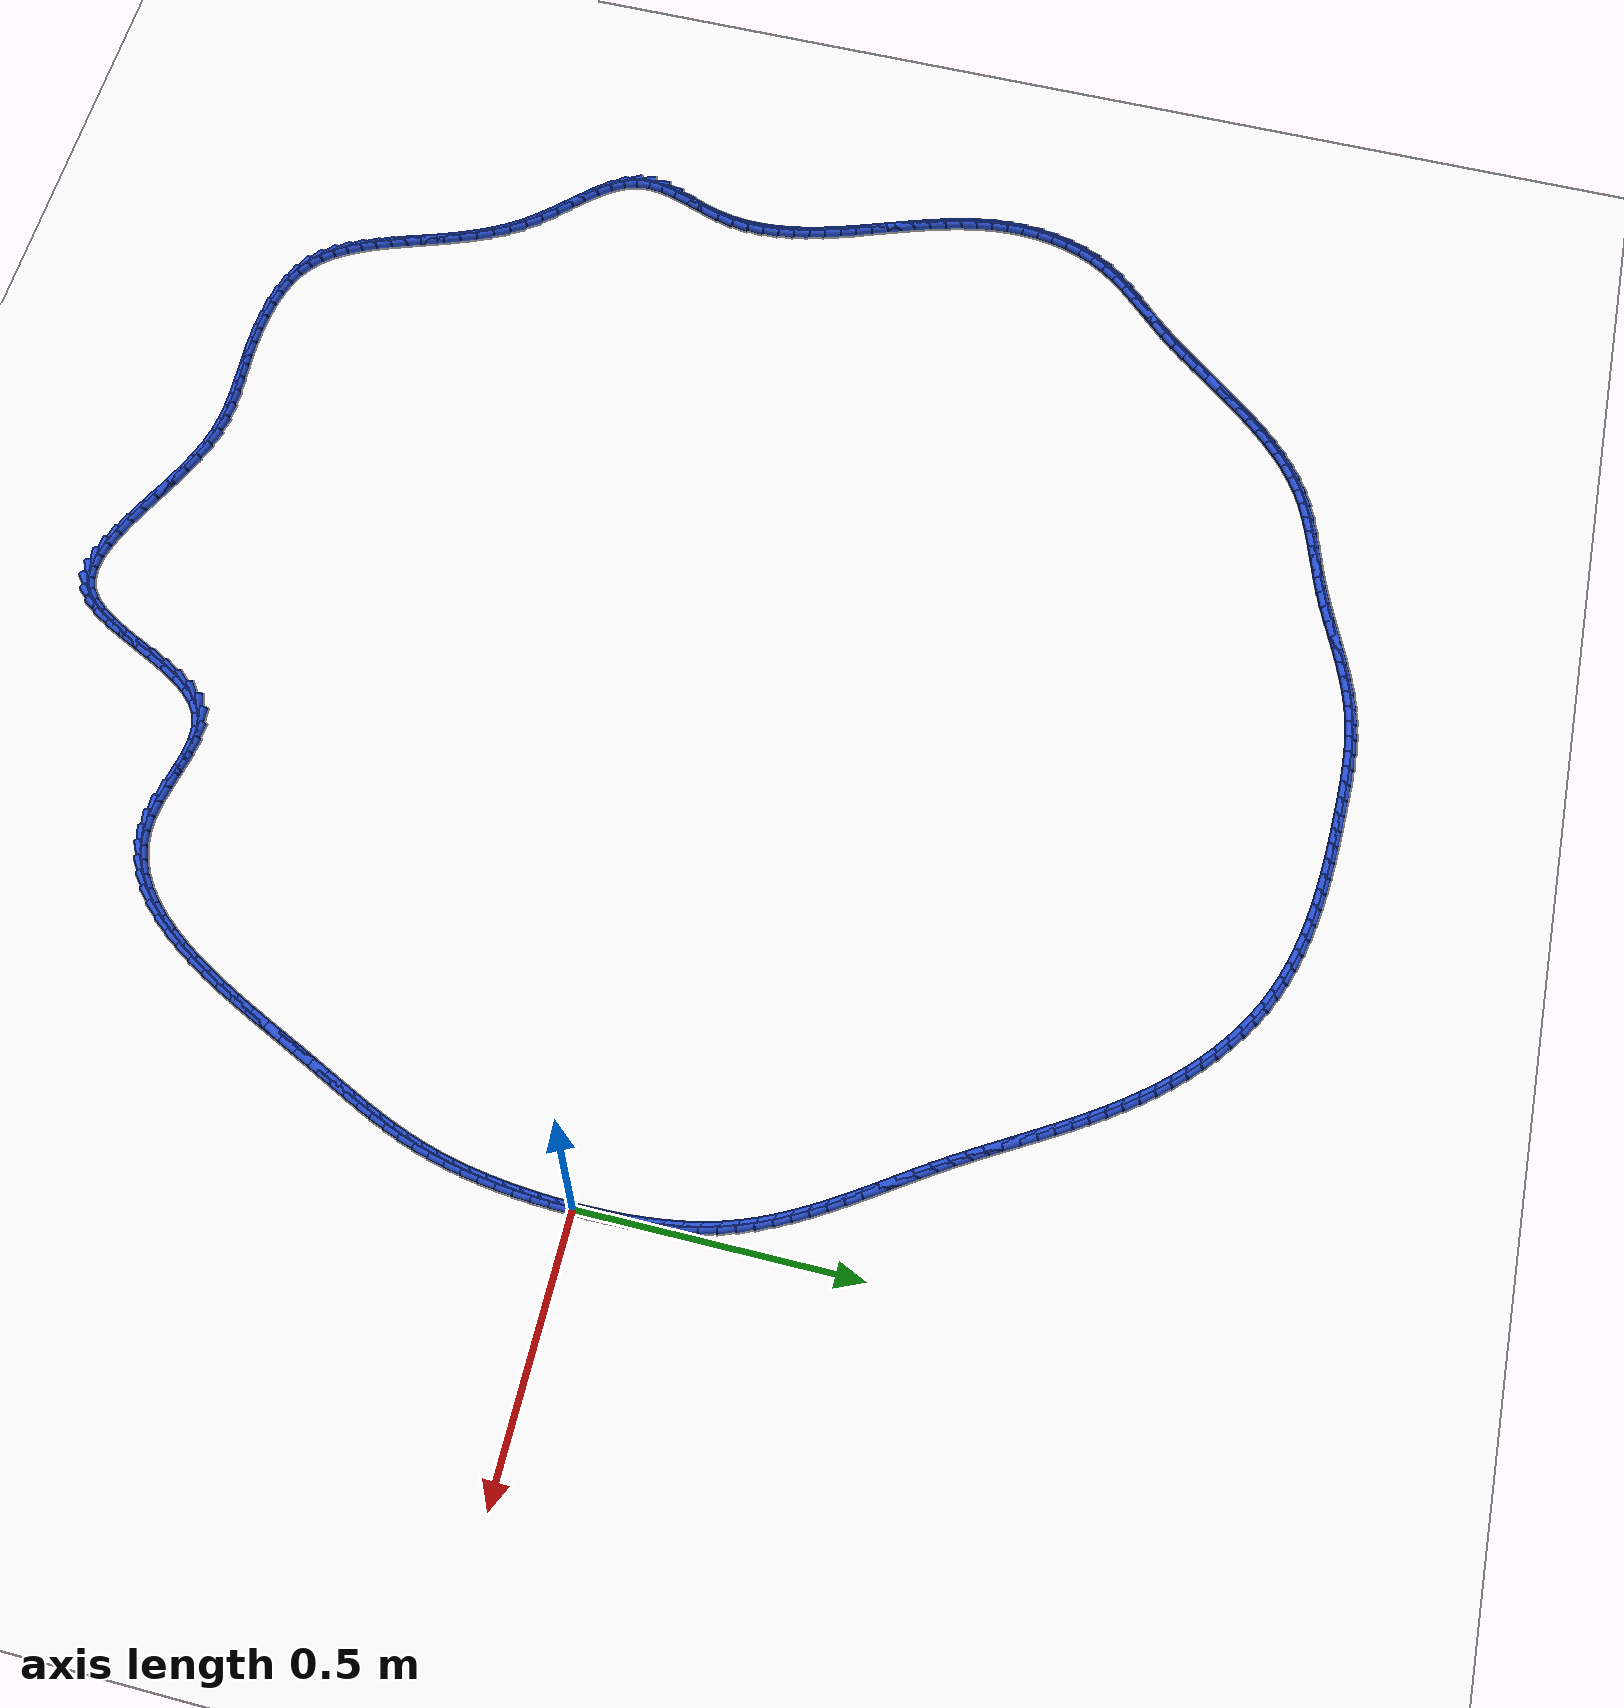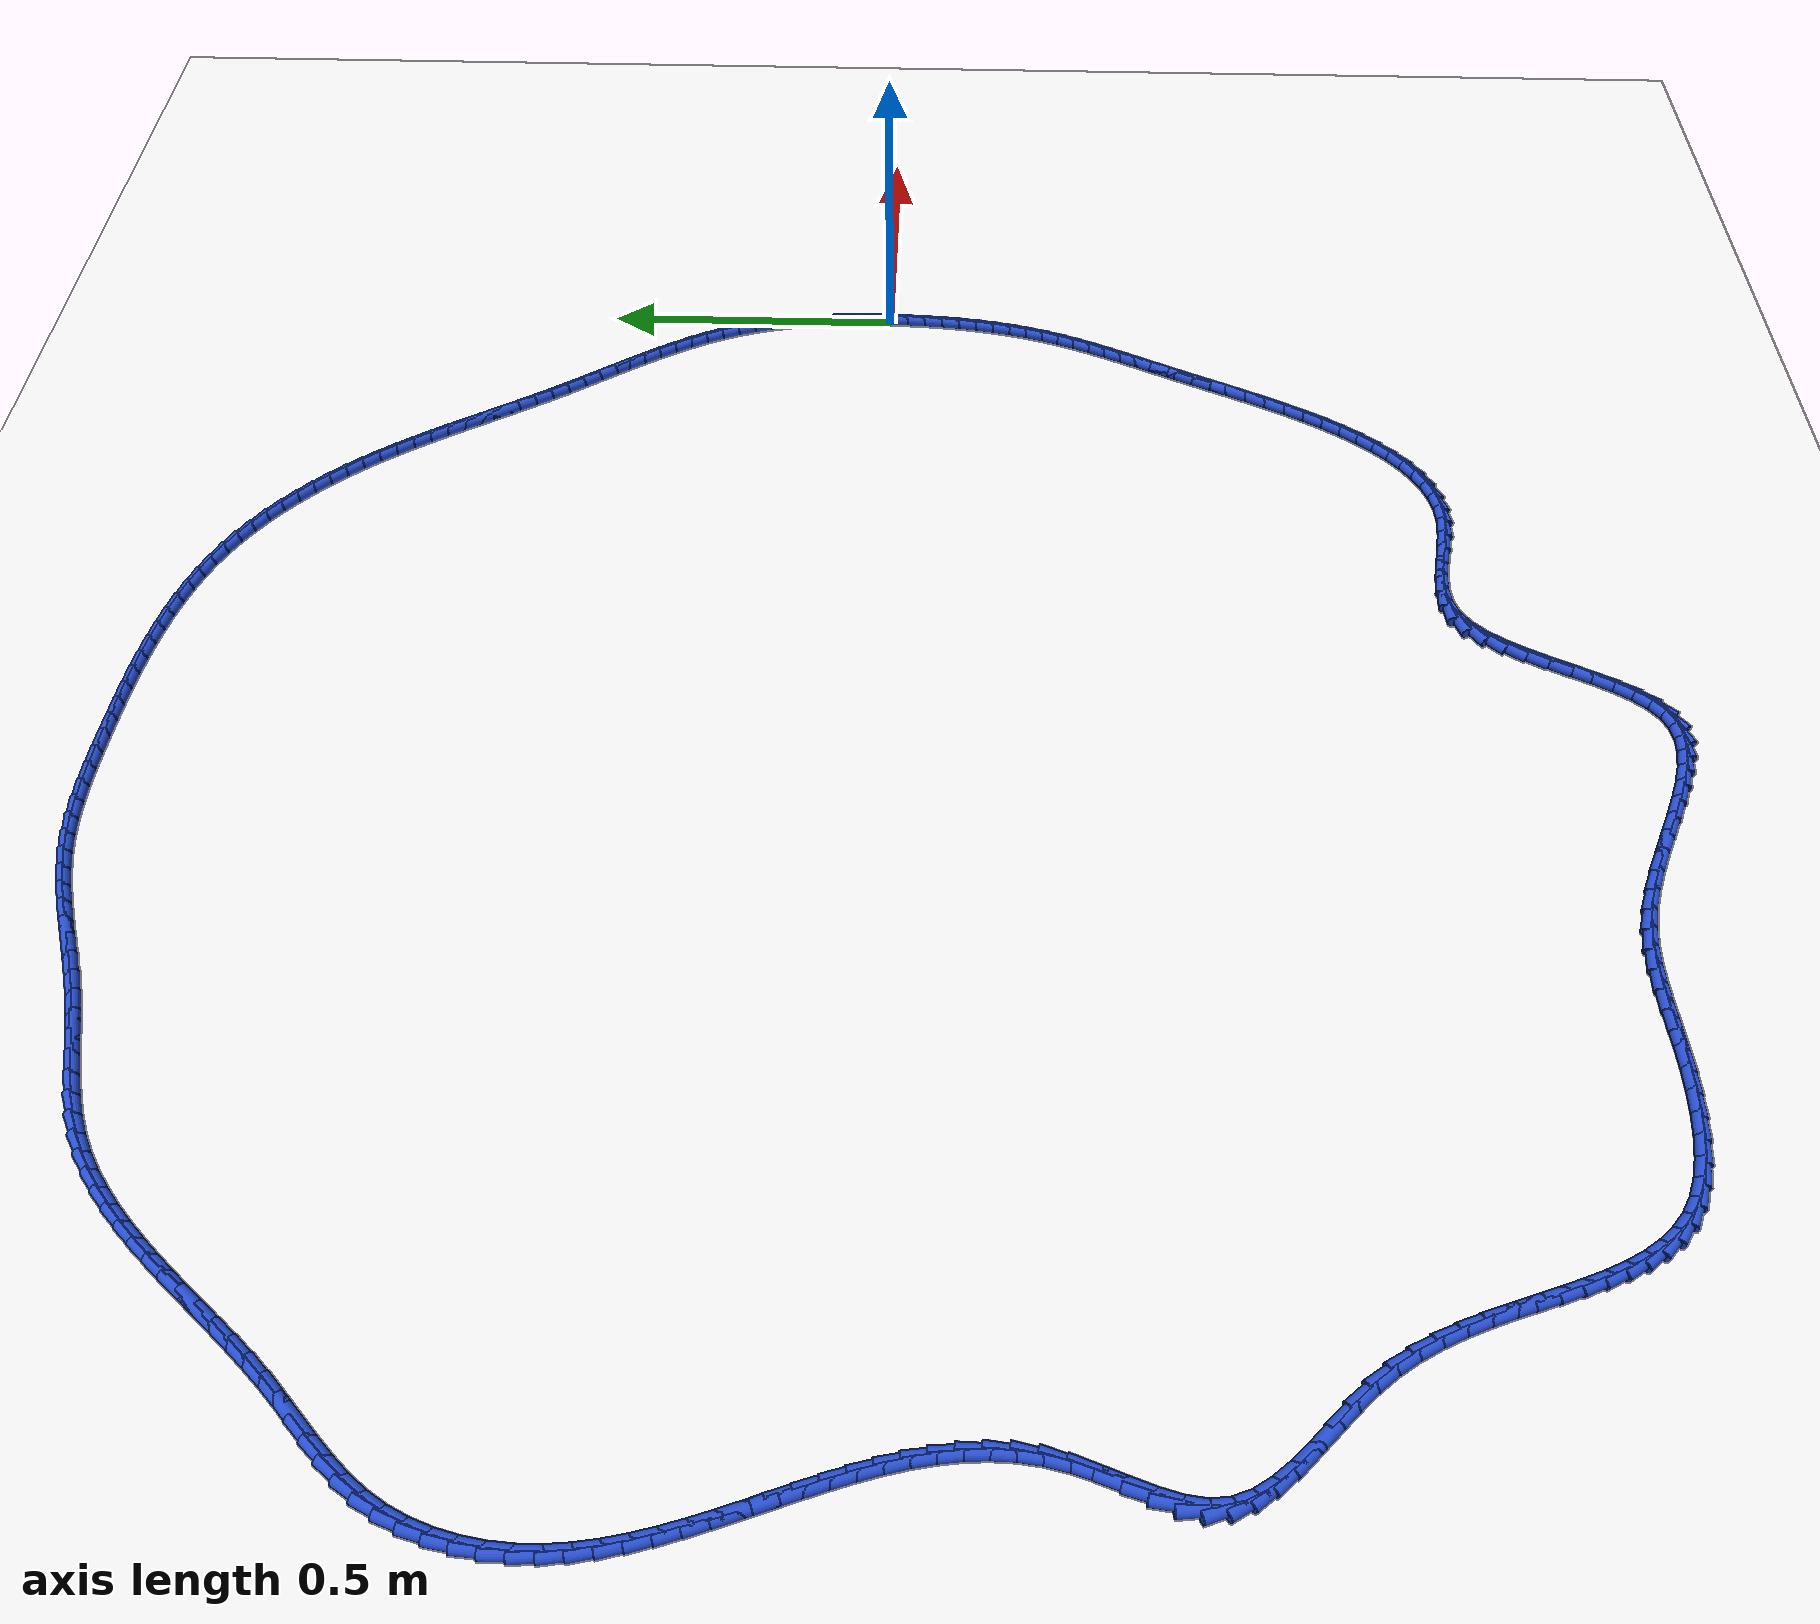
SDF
<sdf version="1.6">
 <world name="default">
  <light name="sun" type="directional">
   <pose>0 0 10 0 -0 0</pose>
   <diffuse>0.8 0.8 0.8 1</diffuse>
   <specular>0.2 0.2 0.2 1</specular>
   <attenuation>
    <range>1000</range>
    <constant>0.9</constant>
    <linear>0.01</linear>
    <quadratic>0.001</quadratic>
   </attenuation>
   <direction>-0.5 0.1 -0.9</direction>
  </light>
  <model name="ground_plane">
   <static>1</static>
   <link name="link">
    <collision name="collision">
     <geometry><plane><normal>0 0 1</normal><size>100 100</size></plane></geometry>
     <surface><friction><ode><mu>100</mu><mu2>50</mu2></ode></friction></surface>
    </collision>
    <visual name="visual">
     <cast_shadows>0</cast_shadows>
     <geometry><plane><normal>0 0 1</normal><size>100 100</size></plane></geometry>
     <material>
      <script><uri>file://media/materials/scripts/gazebo.material</uri><name>Gazebo/WhiteGlow</name></script>
     </material>
    </visual>
   </link>
  </model>
  <gravity>0 0 -9.8</gravity>
  <magnetic_field>6e-06 2.3e-05 -4.2e-05</magnetic_field>
  <atmosphere type="adiabatic"/>
  <physics name="default_physics" default="0" type="ode">
   <max_step_size>0.001</max_step_size>
   <real_time_factor>1</real_time_factor>
   <real_time_update_rate>1000</real_time_update_rate>
  </physics>
  <scene><ambient>0.4 0.4 0.4 1</ambient><background>0.7 0.7 0.7 1</background><shadows>1</shadows></scene>
  <spherical_coordinates>
   <surface_model>EARTH_WGS84</surface_model>
   <latitude_deg>0</latitude_deg>
   <longitude_deg>0</longitude_deg>
   <elevation>0</elevation>
   <heading_deg>0</heading_deg>
  </spherical_coordinates>
  <model name="line">
   <link name="link_0">
    <pose>-1.951563910473908e-17 -4.163336342344337e-17 0.01 0 1.57 1.5705371974184643</pose>
    <collision name="collision">
     <geometry><cylinder><radius>0.01</radius><length>0.08</length></cylinder></geometry>
    </collision>
    <visual name="visual">
     <material>
      <script><name>Gazebo/Blue</name><uri>file://media/materials/scripts/gazebo.material</uri></script>
     </material>
     <geometry><cylinder><radius>0.01</radius><length>0.08</length></cylinder></geometry>
    </visual>
   </link>
   <link name="link_1">
    <pose>8.212343900721934e-06 0.031692059889147944 0.01 0 1.57 -1.544542658793325</pose>
    <collision name="collision">
     <geometry><cylinder><radius>0.01</radius><length>0.08</length></cylinder></geometry>
    </collision>
    <visual name="visual">
     <material>
      <script><name>Gazebo/Blue</name><uri>file://media/materials/scripts/gazebo.material</uri></script>
     </material>
     <geometry><cylinder><radius>0.01</radius><length>0.08</length></cylinder></geometry>
    </visual>
   </link>
   <link name="link_2">
    <pose>-0.0008220711203679883 0.06331022068938982 0.01 0 1.57 -1.5143118049299686</pose>
    <collision name="collision">
     <geometry><cylinder><radius>0.01</radius><length>0.08</length></cylinder></geometry>
    </collision>
    <visual name="visual">
     <material>
      <script><name>Gazebo/Blue</name><uri>file://media/materials/scripts/gazebo.material</uri></script>
     </material>
     <geometry><cylinder><radius>0.01</radius><length>0.08</length></cylinder></geometry>
    </visual>
   </link>
   <link name="link_3">
    <pose>-0.002601419941744138 0.09477824098731115 0.01 0 1.57 -1.4801734309110282</pose>
    <collision name="collision">
     <geometry><cylinder><radius>0.01</radius><length>0.08</length></cylinder></geometry>
    </collision>
    <visual name="visual">
     <material>
      <script><name>Gazebo/Blue</name><uri>file://media/materials/scripts/gazebo.material</uri></script>
     </material>
     <geometry><cylinder><radius>0.01</radius><length>0.08</length></cylinder></geometry>
    </visual>
   </link>
   <link name="link_4">
    <pose>-0.005440403669165712 0.12601987936949752 0.01 0 1.57 -1.4419308487469762</pose>
    <collision name="collision">
     <geometry><cylinder><radius>0.01</radius><length>0.08</length></cylinder></geometry>
    </collision>
    <visual name="visual">
     <material>
      <script><name>Gazebo/Blue</name><uri>file://media/materials/scripts/gazebo.material</uri></script>
     </material>
     <geometry><cylinder><radius>0.01</radius><length>0.08</length></cylinder></geometry>
    </visual>
   </link>
   <link name="link_5">
    <pose>-0.0094495918515707 0.15695889442253444 0.01 0 1.57 -1.3993947894230232</pose>
    <collision name="collision">
     <geometry><cylinder><radius>0.01</radius><length>0.08</length></cylinder></geometry>
    </collision>
    <visual name="visual">
     <material>
      <script><name>Gazebo/Blue</name><uri>file://media/materials/scripts/gazebo.material</uri></script>
     </material>
     <geometry><cylinder><radius>0.01</radius><length>0.08</length></cylinder></geometry>
    </visual>
   </link>
   <link name="link_6">
    <pose>-0.014739554037897094 0.18751904473300757 0.01 0 1.57 -1.3524029153831982</pose>
    <collision name="collision">
     <geometry><cylinder><radius>0.01</radius><length>0.08</length></cylinder></geometry>
    </collision>
    <visual name="visual">
     <material>
      <script><name>Gazebo/Blue</name><uri>file://media/materials/scripts/gazebo.material</uri></script>
     </material>
     <geometry><cylinder><radius>0.01</radius><length>0.08</length></cylinder></geometry>
    </visual>
   </link>
   <link name="link_7">
    <pose>-0.021420859777082874 0.2176240888875024 0.01 0 1.57 -1.3008447680953683</pose>
    <collision name="collision">
     <geometry><cylinder><radius>0.01</radius><length>0.08</length></cylinder></geometry>
    </collision>
    <visual name="visual">
     <material>
      <script><name>Gazebo/Blue</name><uri>file://media/materials/scripts/gazebo.material</uri></script>
     </material>
     <geometry><cylinder><radius>0.01</radius><length>0.08</length></cylinder></geometry>
    </visual>
   </link>
   <link name="link_8">
    <pose>-0.029604078618066028 0.24719778547260457 0.01 0 1.57 -1.2447116623426444</pose>
    <collision name="collision">
     <geometry><cylinder><radius>0.01</radius><length>0.08</length></cylinder></geometry>
    </collision>
    <visual name="visual">
     <material>
      <script><name>Gazebo/Blue</name><uri>file://media/materials/scripts/gazebo.material</uri></script>
     </material>
     <geometry><cylinder><radius>0.01</radius><length>0.08</length></cylinder></geometry>
    </visual>
   </link>
   <link name="link_9">
    <pose>-0.039399236199092365 0.2761641717820654 0.01 0 1.57 -1.1873448098321608</pose>
    <collision name="collision">
     <geometry><cylinder><radius>0.01</radius><length>0.08</length></cylinder></geometry>
    </collision>
    <visual name="visual">
     <material>
      <script><name>Gazebo/Blue</name><uri>file://media/materials/scripts/gazebo.material</uri></script>
     </material>
     <geometry><cylinder><radius>0.01</radius><length>0.08</length></cylinder></geometry>
    </visual>
   </link>
   <link name="link_10">
    <pose>-0.050827574350092074 0.3044927791290657 0.01 0 1.57 -1.1358392322446857</pose>
    <collision name="collision">
     <geometry><cylinder><radius>0.01</radius><length>0.08</length></cylinder></geometry>
    </collision>
    <visual name="visual">
     <material>
      <script><name>Gazebo/Blue</name><uri>file://media/materials/scripts/gazebo.material</uri></script>
     </material>
     <geometry><cylinder><radius>0.01</radius><length>0.08</length></cylinder></geometry>
    </visual>
   </link>
   <link name="link_11">
    <pose>-0.06372391498145809 0.3322486629049067 0.01 0 1.57 -1.0912678068649493</pose>
    <collision name="collision">
     <geometry><cylinder><radius>0.01</radius><length>0.08</length></cylinder></geometry>
    </collision>
    <visual name="visual">
     <material>
      <script><name>Gazebo/Blue</name><uri>file://media/materials/scripts/gazebo.material</uri></script>
     </material>
     <geometry><cylinder><radius>0.01</radius><length>0.08</length></cylinder></geometry>
    </visual>
   </link>
   <link name="link_12">
    <pose>-0.07789957081152395 0.3595089249276038 0.01 0 1.57 -1.0536705645381108</pose>
    <collision name="collision">
     <geometry><cylinder><radius>0.01</radius><length>0.08</length></cylinder></geometry>
    </collision>
    <visual name="visual">
     <material>
      <script><name>Gazebo/Blue</name><uri>file://media/materials/scripts/gazebo.material</uri></script>
     </material>
     <geometry><cylinder><radius>0.01</radius><length>0.08</length></cylinder></geometry>
    </visual>
   </link>
   <link name="link_13">
    <pose>-0.09316585455862321 0.3863506670151728 0.01 0 1.57 -1.0229730755737085</pose>
    <collision name="collision">
     <geometry><cylinder><radius>0.01</radius><length>0.08</length></cylinder></geometry>
    </collision>
    <visual name="visual">
     <material>
      <script><name>Gazebo/Blue</name><uri>file://media/materials/scripts/gazebo.material</uri></script>
     </material>
     <geometry><cylinder><radius>0.01</radius><length>0.08</length></cylinder></geometry>
    </visual>
   </link>
   <link name="link_14">
    <pose>-0.10933407894108954 0.4128509909856296 0.01 0 1.57 -0.9990416596619754</pose>
    <collision name="collision">
     <geometry><cylinder><radius>0.01</radius><length>0.08</length></cylinder></geometry>
    </collision>
    <visual name="visual">
     <material>
      <script><name>Gazebo/Blue</name><uri>file://media/materials/scripts/gazebo.material</uri></script>
     </material>
     <geometry><cylinder><radius>0.01</radius><length>0.08</length></cylinder></geometry>
    </visual>
   </link>
   <link name="link_15">
    <pose>-0.12621555667725648 0.4390869986569897 0.01 0 1.57 -0.9817265611187472</pose>
    <collision name="collision">
     <geometry><cylinder><radius>0.01</radius><length>0.08</length></cylinder></geometry>
    </collision>
    <visual name="visual">
     <material>
      <script><name>Gazebo/Blue</name><uri>file://media/materials/scripts/gazebo.material</uri></script>
     </material>
     <geometry><cylinder><radius>0.01</radius><length>0.08</length></cylinder></geometry>
    </visual>
   </link>
   <link name="link_16">
    <pose>-0.14362160048545763 0.46513579184726883 0.01 0 1.57 -0.9708930663032478</pose>
    <collision name="collision">
     <geometry><cylinder><radius>0.01</radius><length>0.08</length></cylinder></geometry>
    </collision>
    <visual name="visual">
     <material>
      <script><name>Gazebo/Blue</name><uri>file://media/materials/scripts/gazebo.material</uri></script>
     </material>
     <geometry><cylinder><radius>0.01</radius><length>0.08</length></cylinder></geometry>
    </visual>
   </link>
   <link name="link_17">
    <pose>-0.16136352308402657 0.49107447237448265 0.01 0 1.57 -0.9664420455770116</pose>
    <collision name="collision">
     <geometry><cylinder><radius>0.01</radius><length>0.08</length></cylinder></geometry>
    </collision>
    <visual name="visual">
     <material>
      <script><name>Gazebo/Blue</name><uri>file://media/materials/scripts/gazebo.material</uri></script>
     </material>
     <geometry><cylinder><radius>0.01</radius><length>0.08</length></cylinder></geometry>
    </visual>
   </link>
   <link name="link_18">
    <pose>-0.17925263719129692 0.5169801420566469 0.01 0 1.57 -0.9683216995467647</pose>
    <collision name="collision">
     <geometry><cylinder><radius>0.01</radius><length>0.08</length></cylinder></geometry>
    </collision>
    <visual name="visual">
     <material>
      <script><name>Gazebo/Blue</name><uri>file://media/materials/scripts/gazebo.material</uri></script>
     </material>
     <geometry><cylinder><radius>0.01</radius><length>0.08</length></cylinder></geometry>
    </visual>
   </link>
   <link name="link_19">
    <pose>-0.19710025552560217 0.5429299027117773 0.01 0 1.57 -0.976531899796695</pose>
    <collision name="collision">
     <geometry><cylinder><radius>0.01</radius><length>0.08</length></cylinder></geometry>
    </collision>
    <visual name="visual">
     <material>
      <script><name>Gazebo/Blue</name><uri>file://media/materials/scripts/gazebo.material</uri></script>
     </material>
     <geometry><cylinder><radius>0.01</radius><length>0.08</length></cylinder></geometry>
    </visual>
   </link>
   <link name="link_20">
    <pose>-0.21471769080527603 0.5690008561578894 0.01 0 1.57 -0.9908876471693238</pose>
    <collision name="collision">
     <geometry><cylinder><radius>0.01</radius><length>0.08</length></cylinder></geometry>
    </collision>
    <visual name="visual">
     <material>
      <script><name>Gazebo/Blue</name><uri>file://media/materials/scripts/gazebo.material</uri></script>
     </material>
     <geometry><cylinder><radius>0.01</radius><length>0.08</length></cylinder></geometry>
    </visual>
   </link>
   <link name="link_21">
    <pose>-0.23192293053056182 0.5952668764066451 0.01 0 1.57 -1.0061949205408112</pose>
    <collision name="collision">
     <geometry><cylinder><radius>0.01</radius><length>0.08</length></cylinder></geometry>
    </collision>
    <visual name="visual">
     <material>
      <script><name>Gazebo/Blue</name><uri>file://media/materials/scripts/gazebo.material</uri></script>
     </material>
     <geometry><cylinder><radius>0.01</radius><length>0.08</length></cylinder></geometry>
    </visual>
   </link>
   <link name="link_22">
    <pose>-0.24868372511734166 0.6217294147752586 0.01 0 1.57 -1.0172532808980062</pose>
    <collision name="collision">
     <geometry><cylinder><radius>0.01</radius><length>0.08</length></cylinder></geometry>
    </collision>
    <visual name="visual">
     <material>
      <script><name>Gazebo/Blue</name><uri>file://media/materials/scripts/gazebo.material</uri></script>
     </material>
     <geometry><cylinder><radius>0.01</radius><length>0.08</length></cylinder></geometry>
    </visual>
   </link>
   <link name="link_23">
    <pose>-0.26511552990440557 0.6483184950953478 0.01 0 1.57 -1.0238079115313163</pose>
    <collision name="collision">
     <geometry><cylinder><radius>0.01</radius><length>0.08</length></cylinder></geometry>
    </collision>
    <visual name="visual">
     <material>
      <script><name>Gazebo/Blue</name><uri>file://media/materials/scripts/gazebo.material</uri></script>
     </material>
     <geometry><cylinder><radius>0.01</radius><length>0.08</length></cylinder></geometry>
    </visual>
   </link>
   <link name="link_24">
    <pose>-0.28134006338920253 0.6749611124458911 0.01 0 1.57 -1.0258297152912716</pose>
    <collision name="collision">
     <geometry><cylinder><radius>0.01</radius><length>0.08</length></cylinder></geometry>
    </collision>
    <visual name="visual">
     <material>
      <script><name>Gazebo/Blue</name><uri>file://media/materials/scripts/gazebo.material</uri></script>
     </material>
     <geometry><cylinder><radius>0.01</radius><length>0.08</length></cylinder></geometry>
    </visual>
   </link>
   <link name="link_25">
    <pose>-0.2974790440691817 0.7015842619058678 0.01 0 1.57 -1.023291669325934</pose>
    <collision name="collision">
     <geometry><cylinder><radius>0.01</radius><length>0.08</length></cylinder></geometry>
    </collision>
    <visual name="visual">
     <material>
      <script><name>Gazebo/Blue</name><uri>file://media/materials/scripts/gazebo.material</uri></script>
     </material>
     <geometry><cylinder><radius>0.01</radius><length>0.08</length></cylinder></geometry>
    </visual>
   </link>
   <link name="link_26">
    <pose>-0.31365419044179194 0.7281149385542562 0.01 0 1.57 -1.0161676081902289</pose>
    <collision name="collision">
     <geometry><cylinder><radius>0.01</radius><length>0.08</length></cylinder></geometry>
    </collision>
    <visual name="visual">
     <material>
      <script><name>Gazebo/Blue</name><uri>file://media/materials/scripts/gazebo.material</uri></script>
     </material>
     <geometry><cylinder><radius>0.01</radius><length>0.08</length></cylinder></geometry>
    </visual>
   </link>
   <link name="link_27">
    <pose>-0.32998722100448236 0.754480137470036 0.01 0 1.57 -1.0044338532968955</pose>
    <collision name="collision">
     <geometry><cylinder><radius>0.01</radius><length>0.08</length></cylinder></geometry>
    </collision>
    <visual name="visual">
     <material>
      <script><name>Gazebo/Blue</name><uri>file://media/materials/scripts/gazebo.material</uri></script>
     </material>
     <geometry><cylinder><radius>0.01</radius><length>0.08</length></cylinder></geometry>
    </visual>
   </link>
   <link name="link_28">
    <pose>-0.3465998542547019 0.7806068537321855 0.01 0 1.57 -0.9880737951774674</pose>
    <collision name="collision">
     <geometry><cylinder><radius>0.01</radius><length>0.08</length></cylinder></geometry>
    </collision>
    <visual name="visual">
     <material>
      <script><name>Gazebo/Blue</name><uri>file://media/materials/scripts/gazebo.material</uri></script>
     </material>
     <geometry><cylinder><radius>0.01</radius><length>0.08</length></cylinder></geometry>
    </visual>
   </link>
   <link name="link_29">
    <pose>-0.36361380868989973 0.8064220824196837 0.01 0 1.57 -0.9670854911212354</pose>
    <collision name="collision">
     <geometry><cylinder><radius>0.01</radius><length>0.08</length></cylinder></geometry>
    </collision>
    <visual name="visual">
     <material>
      <script><name>Gazebo/Blue</name><uri>file://media/materials/scripts/gazebo.material</uri></script>
     </material>
     <geometry><cylinder><radius>0.01</radius><length>0.08</length></cylinder></geometry>
    </visual>
   </link>
   <link name="link_30">
    <pose>-0.3811508028075249 0.8318528186115097 0.01 0 1.57 -0.9414922213737604</pose>
    <collision name="collision">
     <geometry><cylinder><radius>0.01</radius><length>0.08</length></cylinder></geometry>
    </collision>
    <visual name="visual">
     <material>
      <script><name>Gazebo/Blue</name><uri>file://media/materials/scripts/gazebo.material</uri></script>
     </material>
     <geometry><cylinder><radius>0.01</radius><length>0.08</length></cylinder></geometry>
    </visual>
   </link>
   <link name="link_31">
    <pose>-0.39933255510502613 0.8568260573866422 0.01 0 1.57 -0.9113557052467917</pose>
    <collision name="collision">
     <geometry><cylinder><radius>0.01</radius><length>0.08</length></cylinder></geometry>
    </collision>
    <visual name="visual">
     <material>
      <script><name>Gazebo/Blue</name><uri>file://media/materials/scripts/gazebo.material</uri></script>
     </material>
     <geometry><cylinder><radius>0.01</radius><length>0.08</length></cylinder></geometry>
    </visual>
   </link>
   <link name="link_32">
    <pose>-0.41828078407985286 0.8812687938240603 0.01 0 1.57 -0.8767912798943581</pose>
    <collision name="collision">
     <geometry><cylinder><radius>0.01</radius><length>0.08</length></cylinder></geometry>
    </collision>
    <visual name="visual">
     <material>
      <script><name>Gazebo/Blue</name><uri>file://media/materials/scripts/gazebo.material</uri></script>
     </material>
     <geometry><cylinder><radius>0.01</radius><length>0.08</length></cylinder></geometry>
    </visual>
   </link>
   <link name="link_33">
    <pose>-0.4381172082294539 0.9051080230027428 0.01 0 1.57 -0.8380728673099171</pose>
    <collision name="collision">
     <geometry><cylinder><radius>0.01</radius><length>0.08</length></cylinder></geometry>
    </collision>
    <visual name="visual">
     <material>
      <script><name>Gazebo/Blue</name><uri>file://media/materials/scripts/gazebo.material</uri></script>
     </material>
     <geometry><cylinder><radius>0.01</radius><length>0.08</length></cylinder></geometry>
    </visual>
   </link>
   <link name="link_34">
    <pose>-0.45895771676260955 0.9282684117687956 0.01 0 1.57 -0.7966787297986055</pose>
    <collision name="collision">
     <geometry><cylinder><radius>0.01</radius><length>0.08</length></cylinder></geometry>
    </collision>
    <visual name="visual">
     <material>
      <script><name>Gazebo/Blue</name><uri>file://media/materials/scripts/gazebo.material</uri></script>
     </material>
     <geometry><cylinder><radius>0.01</radius><length>0.08</length></cylinder></geometry>
    </visual>
   </link>
   <link name="link_35">
    <pose>-0.4808293425623125 0.9506391375234833 0.01 0 1.57 -0.7534035131583913</pose>
    <collision name="collision">
     <geometry><cylinder><radius>0.01</radius><length>0.08</length></cylinder></geometry>
    </collision>
    <visual name="visual">
     <material>
      <script><name>Gazebo/Blue</name><uri>file://media/materials/scripts/gazebo.material</uri></script>
     </material>
     <geometry><cylinder><radius>0.01</radius><length>0.08</length></cylinder></geometry>
    </visual>
   </link>
   <link name="link_36">
    <pose>-0.5036898718559039 0.9720817203758696 0.01 0 1.57 -0.7079141387664339</pose>
    <collision name="collision">
     <geometry><cylinder><radius>0.01</radius><length>0.08</length></cylinder></geometry>
    </collision>
    <visual name="visual">
     <material>
      <script><name>Gazebo/Blue</name><uri>file://media/materials/scripts/gazebo.material</uri></script>
     </material>
     <geometry><cylinder><radius>0.01</radius><length>0.08</length></cylinder></geometry>
    </visual>
   </link>
   <link name="link_37">
    <pose>-0.5274952601130616 0.9924569492257043 0.01 0 1.57 -0.6598498970738252</pose>
    <collision name="collision">
     <geometry><cylinder><radius>0.01</radius><length>0.08</length></cylinder></geometry>
    </collision>
    <visual name="visual">
     <material>
      <script><name>Gazebo/Blue</name><uri>file://media/materials/scripts/gazebo.material</uri></script>
     </material>
     <geometry><cylinder><radius>0.01</radius><length>0.08</length></cylinder></geometry>
    </visual>
   </link>
   <link name="link_38">
    <pose>-0.5522014628034622 1.0116256129727346 0.01 0 1.57 -0.6088543799709011</pose>
    <collision name="collision">
     <geometry><cylinder><radius>0.01</radius><length>0.08</length></cylinder></geometry>
    </collision>
    <visual name="visual">
     <material>
      <script><name>Gazebo/Blue</name><uri>file://media/materials/scripts/gazebo.material</uri></script>
     </material>
     <geometry><cylinder><radius>0.01</radius><length>0.08</length></cylinder></geometry>
    </visual>
   </link>
   <link name="link_39">
    <pose>-0.5777644353967838 1.0294485005167109 0.01 0 1.57 -0.5545839367183488</pose>
    <collision name="collision">
     <geometry><cylinder><radius>0.01</radius><length>0.08</length></cylinder></geometry>
    </collision>
    <visual name="visual">
     <material>
      <script><name>Gazebo/Blue</name><uri>file://media/materials/scripts/gazebo.material</uri></script>
     </material>
     <geometry><cylinder><radius>0.01</radius><length>0.08</length></cylinder></geometry>
    </visual>
   </link>
   <link name="link_40">
    <pose>-0.604140133362703 1.045786400757381 0.01 0 1.57 -0.49672518512609604</pose>
    <collision name="collision">
     <geometry><cylinder><radius>0.01</radius><length>0.08</length></cylinder></geometry>
    </collision>
    <visual name="visual">
     <material>
      <script><name>Gazebo/Blue</name><uri>file://media/materials/scripts/gazebo.material</uri></script>
     </material>
     <geometry><cylinder><radius>0.01</radius><length>0.08</length></cylinder></geometry>
    </visual>
   </link>
   <link name="link_41">
    <pose>-0.631284503970598 1.060500221198978 0.01 0 1.57 -0.436921514748377</pose>
    <collision name="collision">
     <geometry><cylinder><radius>0.01</radius><length>0.08</length></cylinder></geometry>
    </collision>
    <visual name="visual">
     <material>
      <script><name>Gazebo/Blue</name><uri>file://media/materials/scripts/gazebo.material</uri></script>
     </material>
     <geometry><cylinder><radius>0.01</radius><length>0.08</length></cylinder></geometry>
    </visual>
   </link>
   <link name="link_42">
    <pose>-0.6591491495447752 1.0735137121696152 0.01 0 1.57 -0.3802907524330635</pose>
    <collision name="collision">
     <geometry><cylinder><radius>0.01</radius><length>0.08</length></cylinder></geometry>
    </collision>
    <visual name="visual">
     <material>
      <script><name>Gazebo/Blue</name><uri>file://media/materials/scripts/gazebo.material</uri></script>
     </material>
     <geometry><cylinder><radius>0.01</radius><length>0.08</length></cylinder></geometry>
    </visual>
   </link>
   <link name="link_43">
    <pose>-0.6876741970585053 1.084916596973423 0.01 0 1.57 -0.3279547343598413</pose>
    <collision name="collision">
     <geometry><cylinder><radius>0.01</radius><length>0.08</length></cylinder></geometry>
    </collision>
    <visual name="visual">
     <material>
      <script><name>Gazebo/Blue</name><uri>file://media/materials/scripts/gazebo.material</uri></script>
     </material>
     <geometry><cylinder><radius>0.01</radius><length>0.08</length></cylinder></geometry>
    </visual>
   </link>
   <link name="link_44">
    <pose>-0.716797900954468 1.0948256821361022 0.01 0 1.57 -0.28009509792888</pose>
    <collision name="collision">
     <geometry><cylinder><radius>0.01</radius><length>0.08</length></cylinder></geometry>
    </collision>
    <visual name="visual">
     <material>
      <script><name>Gazebo/Blue</name><uri>file://media/materials/scripts/gazebo.material</uri></script>
     </material>
     <geometry><cylinder><radius>0.01</radius><length>0.08</length></cylinder></geometry>
    </visual>
   </link>
   <link name="link_45">
    <pose>-0.7464585156753443 1.1033577741833551 0.01 0 1.57 -0.2367782605540357</pose>
    <collision name="collision">
     <geometry><cylinder><radius>0.01</radius><length>0.08</length></cylinder></geometry>
    </collision>
    <visual name="visual">
     <material>
      <script><name>Gazebo/Blue</name><uri>file://media/materials/scripts/gazebo.material</uri></script>
     </material>
     <geometry><cylinder><radius>0.01</radius><length>0.08</length></cylinder></geometry>
    </visual>
   </link>
   <link name="link_46">
    <pose>-0.7765942956638141 1.1106296796408826 0.01 0 1.57 -0.19798361673728448</pose>
    <collision name="collision">
     <geometry><cylinder><radius>0.01</radius><length>0.08</length></cylinder></geometry>
    </collision>
    <visual name="visual">
     <material>
      <script><name>Gazebo/Blue</name><uri>file://media/materials/scripts/gazebo.material</uri></script>
     </material>
     <geometry><cylinder><radius>0.01</radius><length>0.08</length></cylinder></geometry>
    </visual>
   </link>
   <link name="link_47">
    <pose>-0.8071434953625574 1.116758205034386 0.01 0 1.57 -0.16363082136410523</pose>
    <collision name="collision">
     <geometry><cylinder><radius>0.01</radius><length>0.08</length></cylinder></geometry>
    </collision>
    <visual name="visual">
     <material>
      <script><name>Gazebo/Blue</name><uri>file://media/materials/scripts/gazebo.material</uri></script>
     </material>
     <geometry><cylinder><radius>0.01</radius><length>0.08</length></cylinder></geometry>
    </visual>
   </link>
   <link name="link_48">
    <pose>-0.8380443692142551 1.121860156889567 0.01 0 1.57 -0.13360386057045262</pose>
    <collision name="collision">
     <geometry><cylinder><radius>0.01</radius><length>0.08</length></cylinder></geometry>
    </collision>
    <visual name="visual">
     <material>
      <script><name>Gazebo/Blue</name><uri>file://media/materials/scripts/gazebo.material</uri></script>
     </material>
     <geometry><cylinder><radius>0.01</radius><length>0.08</length></cylinder></geometry>
    </visual>
   </link>
   <link name="link_49">
    <pose>-0.8692351716615867 1.1260523417321266 0.01 0 1.57 -0.10777095175089277</pose>
    <collision name="collision">
     <geometry><cylinder><radius>0.01</radius><length>0.08</length></cylinder></geometry>
    </collision>
    <visual name="visual">
     <material>
      <script><name>Gazebo/Blue</name><uri>file://media/materials/scripts/gazebo.material</uri></script>
     </material>
     <geometry><cylinder><radius>0.01</radius><length>0.08</length></cylinder></geometry>
    </visual>
   </link>
   <link name="link_50">
    <pose>-0.9006541571472333 1.1294515660877666 0.01 0 1.57 -0.0860002340974835</pose>
    <collision name="collision">
     <geometry><cylinder><radius>0.01</radius><length>0.08</length></cylinder></geometry>
    </collision>
    <visual name="visual">
     <material>
      <script><name>Gazebo/Blue</name><uri>file://media/materials/scripts/gazebo.material</uri></script>
     </material>
     <geometry><cylinder><radius>0.01</radius><length>0.08</length></cylinder></geometry>
    </visual>
   </link>
   <link name="link_51">
    <pose>-0.9322395801138748 1.1321746364821883 0.01 0 1.57 -0.06817173250397061</pose>
    <collision name="collision">
     <geometry><cylinder><radius>0.01</radius><length>0.08</length></cylinder></geometry>
    </collision>
    <visual name="visual">
     <material>
      <script><name>Gazebo/Blue</name><uri>file://media/materials/scripts/gazebo.material</uri></script>
     </material>
     <geometry><cylinder><radius>0.01</radius><length>0.08</length></cylinder></geometry>
    </visual>
   </link>
   <link name="link_52">
    <pose>-0.9639296950041916 1.1343383594410932 0.01 0 1.57 -0.05418629967276317</pose>
    <collision name="collision">
     <geometry><cylinder><radius>0.01</radius><length>0.08</length></cylinder></geometry>
    </collision>
    <visual name="visual">
     <material>
      <script><name>Gazebo/Blue</name><uri>file://media/materials/scripts/gazebo.material</uri></script>
     </material>
     <geometry><cylinder><radius>0.01</radius><length>0.08</length></cylinder></geometry>
    </visual>
   </link>
   <link name="link_53">
    <pose>-0.9956627562608634 1.136059541490182 0.01 0 1.57 -0.0439722719032757</pose>
    <collision name="collision">
     <geometry><cylinder><radius>0.01</radius><length>0.08</length></cylinder></geometry>
    </collision>
    <visual name="visual">
     <material>
      <script><name>Gazebo/Blue</name><uri>file://media/materials/scripts/gazebo.material</uri></script>
     </material>
     <geometry><cylinder><radius>0.01</radius><length>0.08</length></cylinder></geometry>
    </visual>
   </link>
   <link name="link_54">
    <pose>-1.0273770183265716 1.1374549891551569 0.01 0 1.57 -0.03554836688999571</pose>
    <collision name="collision">
     <geometry><cylinder><radius>0.01</radius><length>0.08</length></cylinder></geometry>
    </collision>
    <visual name="visual">
     <material>
      <script><name>Gazebo/Blue</name><uri>file://media/materials/scripts/gazebo.material</uri></script>
     </material>
     <geometry><cylinder><radius>0.01</radius><length>0.08</length></cylinder></geometry>
    </visual>
   </link>
   <link name="link_55">
    <pose>-1.059011893011788 1.1385800312270324 0.01 0 1.57 -0.020784394344310016</pose>
    <collision name="collision">
     <geometry><cylinder><radius>0.01</radius><length>0.08</length></cylinder></geometry>
    </collision>
    <visual name="visual">
     <material>
      <script><name>Gazebo/Blue</name><uri>file://media/materials/scripts/gazebo.material</uri></script>
     </material>
     <geometry><cylinder><radius>0.01</radius><length>0.08</length></cylinder></geometry>
    </visual>
   </link>
   <link name="link_56">
    <pose>-1.0905115958835596 1.139234827764711 0.01 0 1.57 0.0026024233260266033</pose>
    <collision name="collision">
     <geometry><cylinder><radius>0.01</radius><length>0.08</length></cylinder></geometry>
    </collision>
    <visual name="visual">
     <material>
      <script><name>Gazebo/Blue</name><uri>file://media/materials/scripts/gazebo.material</uri></script>
     </material>
     <geometry><cylinder><radius>0.01</radius><length>0.08</length></cylinder></geometry>
    </visual>
   </link>
   <link name="link_57">
    <pose>-1.1218215886473055 1.1391533457252563 0.01 0 1.57 0.03487295807938544</pose>
    <collision name="collision">
     <geometry><cylinder><radius>0.01</radius><length>0.08</length></cylinder></geometry>
    </collision>
    <visual name="visual">
     <material>
      <script><name>Gazebo/Blue</name><uri>file://media/materials/scripts/gazebo.material</uri></script>
     </material>
     <geometry><cylinder><radius>0.01</radius><length>0.08</length></cylinder></geometry>
    </visual>
   </link>
   <link name="link_58">
    <pose>-1.1528873330106877 1.1380695519464887 0.01 0 1.57 0.07630173418979681</pose>
    <collision name="collision">
     <geometry><cylinder><radius>0.01</radius><length>0.08</length></cylinder></geometry>
    </collision>
    <visual name="visual">
     <material>
      <script><name>Gazebo/Blue</name><uri>file://media/materials/scripts/gazebo.material</uri></script>
     </material>
     <geometry><cylinder><radius>0.01</radius><length>0.08</length></cylinder></geometry>
    </visual>
   </link>
   <link name="link_59">
    <pose>-1.1836542906813696 1.1357174132662293 0.01 0 1.57 0.12709978297195684</pose>
    <collision name="collision">
     <geometry><cylinder><radius>0.01</radius><length>0.08</length></cylinder></geometry>
    </collision>
    <visual name="visual">
     <material>
      <script><name>Gazebo/Blue</name><uri>file://media/materials/scripts/gazebo.material</uri></script>
     </material>
     <geometry><cylinder><radius>0.01</radius><length>0.08</length></cylinder></geometry>
    </visual>
   </link>
   <link name="link_60">
    <pose>-1.2140679233670135 1.1318308965222994 0.01 0 1.57 0.18727788384975455</pose>
    <collision name="collision">
     <geometry><cylinder><radius>0.01</radius><length>0.08</length></cylinder></geometry>
    </collision>
    <visual name="visual">
     <material>
      <script><name>Gazebo/Blue</name><uri>file://media/materials/scripts/gazebo.material</uri></script>
     </material>
     <geometry><cylinder><radius>0.01</radius><length>0.08</length></cylinder></geometry>
    </visual>
   </link>
   <link name="link_61">
    <pose>-1.2440739061980506 1.1261448075220017 0.01 0 1.57 0.25048885633698287</pose>
    <collision name="collision">
     <geometry><cylinder><radius>0.01</radius><length>0.08</length></cylinder></geometry>
    </collision>
    <visual name="visual">
     <material>
      <script><name>Gazebo/Blue</name><uri>file://media/materials/scripts/gazebo.material</uri></script>
     </material>
     <geometry><cylinder><radius>0.01</radius><length>0.08</length></cylinder></geometry>
    </visual>
   </link>
   <link name="link_62">
    <pose>-1.2736636870780544 1.118573885826262 0.01 0 1.57 0.3026504630328607</pose>
    <collision name="collision">
     <geometry><cylinder><radius>0.01</radius><length>0.08</length></cylinder></geometry>
    </collision>
    <visual name="visual">
     <material>
      <script><name>Gazebo/Blue</name><uri>file://media/materials/scripts/gazebo.material</uri></script>
     </material>
     <geometry><cylinder><radius>0.01</radius><length>0.08</length></cylinder></geometry>
    </visual>
   </link>
   <link name="link_63">
    <pose>-1.3029310991111553 1.109435349416834 0.01 0 1.57 0.34175123564545307</pose>
    <collision name="collision">
     <geometry><cylinder><radius>0.01</radius><length>0.08</length></cylinder></geometry>
    </collision>
    <visual name="visual">
     <material>
      <script><name>Gazebo/Blue</name><uri>file://media/materials/scripts/gazebo.material</uri></script>
     </material>
     <geometry><cylinder><radius>0.01</radius><length>0.08</length></cylinder></geometry>
    </visual>
   </link>
   <link name="link_64">
    <pose>-1.3319838691904278 1.099101033058015 0.01 0 1.57 0.36793322855585825</pose>
    <collision name="collision">
     <geometry><cylinder><radius>0.01</radius><length>0.08</length></cylinder></geometry>
    </collision>
    <visual name="visual">
     <material>
      <script><name>Gazebo/Blue</name><uri>file://media/materials/scripts/gazebo.material</uri></script>
     </material>
     <geometry><cylinder><radius>0.01</radius><length>0.08</length></cylinder></geometry>
    </visual>
   </link>
   <link name="link_65">
    <pose>-1.360929724208948 1.087942771514102 0.01 0 1.57 0.3814502427005455</pose>
    <collision name="collision">
     <geometry><cylinder><radius>0.01</radius><length>0.08</length></cylinder></geometry>
    </collision>
    <visual name="visual">
     <material>
      <script><name>Gazebo/Blue</name><uri>file://media/materials/scripts/gazebo.material</uri></script>
     </material>
     <geometry><cylinder><radius>0.01</radius><length>0.08</length></cylinder></geometry>
    </visual>
   </link>
   <link name="link_66">
    <pose>-1.3898763910597918 1.0763323995493908 0.01 0 1.57 0.38253905778734415</pose>
    <collision name="collision">
     <geometry><cylinder><radius>0.01</radius><length>0.08</length></cylinder></geometry>
    </collision>
    <visual name="visual">
     <material>
      <script><name>Gazebo/Blue</name><uri>file://media/materials/scripts/gazebo.material</uri></script>
     </material>
     <geometry><cylinder><radius>0.01</radius><length>0.08</length></cylinder></geometry>
    </visual>
   </link>
   <link name="link_67">
    <pose>-1.4189315966360343 1.0646417519281797 0.01 0 1.57 0.3713582480179132</pose>
    <collision name="collision">
     <geometry><cylinder><radius>0.01</radius><length>0.08</length></cylinder></geometry>
    </collision>
    <visual name="visual">
     <material>
      <script><name>Gazebo/Blue</name><uri>file://media/materials/scripts/gazebo.material</uri></script>
     </material>
     <geometry><cylinder><radius>0.01</radius><length>0.08</length></cylinder></geometry>
    </visual>
   </link>
   <link name="link_68">
    <pose>-1.448203067830752 1.053242663414765 0.01 0 1.57 0.34798614795337746</pose>
    <collision name="collision">
     <geometry><cylinder><radius>0.01</radius><length>0.08</length></cylinder></geometry>
    </collision>
    <visual name="visual">
     <material>
      <script><name>Gazebo/Blue</name><uri>file://media/materials/scripts/gazebo.material</uri></script>
     </material>
     <geometry><cylinder><radius>0.01</radius><length>0.08</length></cylinder></geometry>
    </visual>
   </link>
   <link name="link_69">
    <pose>-1.4777985315370201 1.0425069687734438 0.01 0 1.57 0.31504509297339006</pose>
    <collision name="collision">
     <geometry><cylinder><radius>0.01</radius><length>0.08</length></cylinder></geometry>
    </collision>
    <visual name="visual">
     <material>
      <script><name>Gazebo/Blue</name><uri>file://media/materials/scripts/gazebo.material</uri></script>
     </material>
     <geometry><cylinder><radius>0.01</radius><length>0.08</length></cylinder></geometry>
    </visual>
   </link>
   <link name="link_70">
    <pose>-1.5077925427802419 1.0327319407440556 0.01 0 1.57 0.29158548764364767</pose>
    <collision name="collision">
     <geometry><cylinder><radius>0.01</radius><length>0.08</length></cylinder></geometry>
    </collision>
    <visual name="visual">
     <material>
      <script><name>Gazebo/Blue</name><uri>file://media/materials/scripts/gazebo.material</uri></script>
     </material>
     <geometry><cylinder><radius>0.01</radius><length>0.08</length></cylinder></geometry>
    </visual>
   </link>
   <link name="link_71">
    <pose>-1.5380134451496255 1.0236614306158194 0.01 0 1.57 0.2860192500326317</pose>
    <collision name="collision">
     <geometry><cylinder><radius>0.01</radius><length>0.08</length></cylinder></geometry>
    </collision>
    <visual name="visual">
     <material>
      <script><name>Gazebo/Blue</name><uri>file://media/materials/scripts/gazebo.material</uri></script>
     </material>
     <geometry><cylinder><radius>0.01</radius><length>0.08</length></cylinder></geometry>
    </visual>
   </link>
   <link name="link_72">
    <pose>-1.5681788170912774 1.0147903174647928 0.01 0 1.57 0.2985150818508363</pose>
    <collision name="collision">
     <geometry><cylinder><radius>0.01</radius><length>0.08</length></cylinder></geometry>
    </collision>
    <visual name="visual">
     <material>
      <script><name>Gazebo/Blue</name><uri>file://media/materials/scripts/gazebo.material</uri></script>
     </material>
     <geometry><cylinder><radius>0.01</radius><length>0.08</length></cylinder></geometry>
    </visual>
   </link>
   <link name="link_73">
    <pose>-1.598005705674188 1.0056122859647871 0.01 0 1.57 0.3296221462535409</pose>
    <collision name="collision">
     <geometry><cylinder><radius>0.01</radius><length>0.08</length></cylinder></geometry>
    </collision>
    <visual name="visual">
     <material>
      <script><name>Gazebo/Blue</name><uri>file://media/materials/scripts/gazebo.material</uri></script>
     </material>
     <geometry><cylinder><radius>0.01</radius><length>0.08</length></cylinder></geometry>
    </visual>
   </link>
   <link name="link_74">
    <pose>-1.627211157967352 0.9956210207896149 0.01 0 1.57 0.38021358386515425</pose>
    <collision name="collision">
     <geometry><cylinder><radius>0.01</radius><length>0.08</length></cylinder></geometry>
    </collision>
    <visual name="visual">
     <material>
      <script><name>Gazebo/Blue</name><uri>file://media/materials/scripts/gazebo.material</uri></script>
     </material>
     <geometry><cylinder><radius>0.01</radius><length>0.08</length></cylinder></geometry>
    </visual>
   </link>
   <link name="link_75">
    <pose>-1.6555122210397601 0.9843102066130873 0.01 0 1.57 0.451069140959367</pose>
    <collision name="collision">
     <geometry><cylinder><radius>0.01</radius><length>0.08</length></cylinder></geometry>
    </collision>
    <visual name="visual">
     <material>
      <script><name>Gazebo/Blue</name><uri>file://media/materials/scripts/gazebo.material</uri></script>
     </material>
     <geometry><cylinder><radius>0.01</radius><length>0.08</length></cylinder></geometry>
    </visual>
   </link>
   <link name="link_76">
    <pose>-1.6826275519774485 0.9711762354318262 0.01 0 1.57 0.533100362238966</pose>
    <collision name="collision">
     <geometry><cylinder><radius>0.01</radius><length>0.08</length></cylinder></geometry>
    </collision>
    <visual name="visual">
     <material>
      <script><name>Gazebo/Blue</name><uri>file://media/materials/scripts/gazebo.material</uri></script>
     </material>
     <geometry><cylinder><radius>0.01</radius><length>0.08</length></cylinder></geometry>
    </visual>
   </link>
   <link name="link_77">
    <pose>-1.7084193053329146 0.9559567972869695 0.01 0 1.57 0.6088000227474032</pose>
    <collision name="collision">
     <geometry><cylinder><radius>0.01</radius><length>0.08</length></cylinder></geometry>
    </collision>
    <visual name="visual">
     <material>
      <script><name>Gazebo/Blue</name><uri>file://media/materials/scripts/gazebo.material</uri></script>
     </material>
     <geometry><cylinder><radius>0.01</radius><length>0.08</length></cylinder></geometry>
    </visual>
   </link>
   <link name="link_78">
    <pose>-1.7330042763302742 0.9388177730277011 0.01 0 1.57 0.6755655785510147</pose>
    <collision name="collision">
     <geometry><cylinder><radius>0.01</radius><length>0.08</length></cylinder></geometry>
    </collision>
    <visual name="visual">
     <material>
      <script><name>Gazebo/Blue</name><uri>file://media/materials/scripts/gazebo.material</uri></script>
     </material>
     <geometry><cylinder><radius>0.01</radius><length>0.08</length></cylinder></geometry>
    </visual>
   </link>
   <link name="link_79">
    <pose>-1.7565254177860383 0.9199690287807802 0.01 0 1.57 0.7330194291430522</pose>
    <collision name="collision">
     <geometry><cylinder><radius>0.01</radius><length>0.08</length></cylinder></geometry>
    </collision>
    <visual name="visual">
     <material>
      <script><name>Gazebo/Blue</name><uri>file://media/materials/scripts/gazebo.material</uri></script>
     </material>
     <geometry><cylinder><radius>0.01</radius><length>0.08</length></cylinder></geometry>
    </visual>
   </link>
   <link name="link_80">
    <pose>-1.7791256825167177 0.8996204306729682 0.01 0 1.57 0.7811701383800754</pose>
    <collision name="collision">
     <geometry><cylinder><radius>0.01</radius><length>0.08</length></cylinder></geometry>
    </collision>
    <visual name="visual">
     <material>
      <script><name>Gazebo/Blue</name><uri>file://media/materials/scripts/gazebo.material</uri></script>
     </material>
     <geometry><cylinder><radius>0.01</radius><length>0.08</length></cylinder></geometry>
    </visual>
   </link>
   <link name="link_81">
    <pose>-1.8009480233388229 0.8779818448310247 0.01 0 1.57 0.82026161148353</pose>
    <collision name="collision">
     <geometry><cylinder><radius>0.01</radius><length>0.08</length></cylinder></geometry>
    </collision>
    <visual name="visual">
     <material>
      <script><name>Gazebo/Blue</name><uri>file://media/materials/scripts/gazebo.material</uri></script>
     </material>
     <geometry><cylinder><radius>0.01</radius><length>0.08</length></cylinder></geometry>
    </visual>
   </link>
   <link name="link_82">
    <pose>-1.8221353930688644 0.85526313738171 0.01 0 1.57 0.8506470874871135</pose>
    <collision name="collision">
     <geometry><cylinder><radius>0.01</radius><length>0.08</length></cylinder></geometry>
    </collision>
    <visual name="visual">
     <material>
      <script><name>Gazebo/Blue</name><uri>file://media/materials/scripts/gazebo.material</uri></script>
     </material>
     <geometry><cylinder><radius>0.01</radius><length>0.08</length></cylinder></geometry>
    </visual>
   </link>
   <link name="link_83">
    <pose>-1.8428307445233527 0.8316741744517838 0.01 0 1.57 0.8726969711150186</pose>
    <collision name="collision">
     <geometry><cylinder><radius>0.01</radius><length>0.08</length></cylinder></geometry>
    </collision>
    <visual name="visual">
     <material>
      <script><name>Gazebo/Blue</name><uri>file://media/materials/scripts/gazebo.material</uri></script>
     </material>
     <geometry><cylinder><radius>0.01</radius><length>0.08</length></cylinder></geometry>
    </visual>
   </link>
   <link name="link_84">
    <pose>-1.8631770305187996 0.8074248221680073 0.01 0 1.57 0.8867379826410885</pose>
    <collision name="collision">
     <geometry><cylinder><radius>0.01</radius><length>0.08</length></cylinder></geometry>
    </collision>
    <visual name="visual">
     <material>
      <script><name>Gazebo/Blue</name><uri>file://media/materials/scripts/gazebo.material</uri></script>
     </material>
     <geometry><cylinder><radius>0.01</radius><length>0.08</length></cylinder></geometry>
    </visual>
   </link>
   <link name="link_85">
    <pose>-1.8833172038717145 0.7827249466571395 0.01 0 1.57 0.8930168347767435</pose>
    <collision name="collision">
     <geometry><cylinder><radius>0.01</radius><length>0.08</length></cylinder></geometry>
    </collision>
    <visual name="visual">
     <material>
      <script><name>Gazebo/Blue</name><uri>file://media/materials/scripts/gazebo.material</uri></script>
     </material>
     <geometry><cylinder><radius>0.01</radius><length>0.08</length></cylinder></geometry>
    </visual>
   </link>
   <link name="link_86">
    <pose>-1.9033942173986085 0.7577844140459415 0.01 0 1.57 0.8916816464733052</pose>
    <collision name="collision">
     <geometry><cylinder><radius>0.01</radius><length>0.08</length></cylinder></geometry>
    </collision>
    <visual name="visual">
     <material>
      <script><name>Gazebo/Blue</name><uri>file://media/materials/scripts/gazebo.material</uri></script>
     </material>
     <geometry><cylinder><radius>0.01</radius><length>0.08</length></cylinder></geometry>
    </visual>
   </link>
   <link name="link_87">
    <pose>-1.9235510239159919 0.7328130904611729 0.01 0 1.57 0.8827761613719337</pose>
    <collision name="collision">
     <geometry><cylinder><radius>0.01</radius><length>0.08</length></cylinder></geometry>
    </collision>
    <visual name="visual">
     <material>
      <script><name>Gazebo/Blue</name><uri>file://media/materials/scripts/gazebo.material</uri></script>
     </material>
     <geometry><cylinder><radius>0.01</radius><length>0.08</length></cylinder></geometry>
    </visual>
   </link>
   <link name="link_88">
    <pose>-1.9439305762403756 0.7080208420295938 0.01 0 1.57 0.8662442212478744</pose>
    <collision name="collision">
     <geometry><cylinder><radius>0.01</radius><length>0.08</length></cylinder></geometry>
    </collision>
    <visual name="visual">
     <material>
      <script><name>Gazebo/Blue</name><uri>file://media/materials/scripts/gazebo.material</uri></script>
     </material>
     <geometry><cylinder><radius>0.01</radius><length>0.08</length></cylinder></geometry>
    </visual>
   </link>
   <link name="link_89">
    <pose>-1.96467582718827 0.6836175348779648 0.01 0 1.57 0.841944294083444</pose>
    <collision name="collision">
     <geometry><cylinder><radius>0.01</radius><length>0.08</length></cylinder></geometry>
    </collision>
    <visual name="visual">
     <material>
      <script><name>Gazebo/Blue</name><uri>file://media/materials/scripts/gazebo.material</uri></script>
     </material>
     <geometry><cylinder><radius>0.01</radius><length>0.08</length></cylinder></geometry>
    </visual>
   </link>
   <link name="link_90">
    <pose>-1.9859297295761866 0.6598130351330457 0.01 0 1.57 0.810487327405514</pose>
    <collision name="collision">
     <geometry><cylinder><radius>0.01</radius><length>0.08</length></cylinder></geometry>
    </collision>
    <visual name="visual">
     <material>
      <script><name>Gazebo/Blue</name><uri>file://media/materials/scripts/gazebo.material</uri></script>
     </material>
     <geometry><cylinder><radius>0.01</radius><length>0.08</length></cylinder></geometry>
    </visual>
   </link>
   <link name="link_91">
    <pose>-2.0078166730612454 0.6367993356236505 0.01 0 1.57 0.7876126604401993</pose>
    <collision name="collision">
     <geometry><cylinder><radius>0.01</radius><length>0.08</length></cylinder></geometry>
    </collision>
    <visual name="visual">
     <material>
      <script><name>Gazebo/Blue</name><uri>file://media/materials/scripts/gazebo.material</uri></script>
     </material>
     <geometry><cylinder><radius>0.01</radius><length>0.08</length></cylinder></geometry>
    </visual>
   </link>
   <link name="link_92">
    <pose>-2.0300981178569164 0.6144189872574243 0.01 0 1.57 0.7880123809386074</pose>
    <collision name="collision">
     <geometry><cylinder><radius>0.01</radius><length>0.08</length></cylinder></geometry>
    </collision>
    <visual name="visual">
     <material>
      <script><name>Gazebo/Blue</name><uri>file://media/materials/scripts/gazebo.material</uri></script>
     </material>
     <geometry><cylinder><radius>0.01</radius><length>0.08</length></cylinder></geometry>
    </visual>
   </link>
   <link name="link_93">
    <pose>-2.0522049580726587 0.5921962596438739 0.01 0 1.57 0.8127559860994664</pose>
    <collision name="collision">
     <geometry><cylinder><radius>0.01</radius><length>0.08</length></cylinder></geometry>
    </collision>
    <visual name="visual">
     <material>
      <script><name>Gazebo/Blue</name><uri>file://media/materials/scripts/gazebo.material</uri></script>
     </material>
     <geometry><cylinder><radius>0.01</radius><length>0.08</length></cylinder></geometry>
    </visual>
   </link>
   <link name="link_94">
    <pose>-2.0735560150328456 0.5696437982675207 0.01 0 1.57 0.8625882593590323</pose>
    <collision name="collision">
     <geometry><cylinder><radius>0.01</radius><length>0.08</length></cylinder></geometry>
    </collision>
    <visual name="visual">
     <material>
      <script><name>Gazebo/Blue</name><uri>file://media/materials/scripts/gazebo.material</uri></script>
     </material>
     <geometry><cylinder><radius>0.01</radius><length>0.08</length></cylinder></geometry>
    </visual>
   </link>
   <link name="link_95">
    <pose>-2.0935701100618527 0.5462742486128869 0.01 0 1.57 0.9380028660981233</pose>
    <collision name="collision">
     <geometry><cylinder><radius>0.01</radius><length>0.08</length></cylinder></geometry>
    </collision>
    <visual name="visual">
     <material>
      <script><name>Gazebo/Blue</name><uri>file://media/materials/scripts/gazebo.material</uri></script>
     </material>
     <geometry><cylinder><radius>0.01</radius><length>0.08</length></cylinder></geometry>
    </visual>
   </link>
   <link name="link_96">
    <pose>-2.111666064484053 0.5216002561644936 0.01 0 1.57 1.0372943485846446</pose>
    <collision name="collision">
     <geometry><cylinder><radius>0.01</radius><length>0.08</length></cylinder></geometry>
    </collision>
    <visual name="visual">
     <material>
      <script><name>Gazebo/Blue</name><uri>file://media/materials/scripts/gazebo.material</uri></script>
     </material>
     <geometry><cylinder><radius>0.01</radius><length>0.08</length></cylinder></geometry>
    </visual>
   </link>
   <link name="link_97">
    <pose>-2.127281690092182 0.49516136612256145 0.01 0 1.57 1.142192403774082</pose>
    <collision name="collision">
     <geometry><cylinder><radius>0.01</radius><length>0.08</length></cylinder></geometry>
    </collision>
    <visual name="visual">
     <material>
      <script><name>Gazebo/Blue</name><uri>file://media/materials/scripts/gazebo.material</uri></script>
     </material>
     <geometry><cylinder><radius>0.01</radius><length>0.08</length></cylinder></geometry>
    </visual>
   </link>
   <link name="link_98">
    <pose>-2.14017321781707 0.46694815965575537 0.01 0 1.57 1.2395602424939434</pose>
    <collision name="collision">
     <geometry><cylinder><radius>0.01</radius><length>0.08</length></cylinder></geometry>
    </collision>
    <visual name="visual">
     <material>
      <script><name>Gazebo/Blue</name><uri>file://media/materials/scripts/gazebo.material</uri></script>
     </material>
     <geometry><cylinder><radius>0.01</radius><length>0.08</length></cylinder></geometry>
    </visual>
   </link>
   <link name="link_99">
    <pose>-2.150360797673426 0.43732505538578603 0.01 0 1.57 1.3305070578912288</pose>
    <collision name="collision">
     <geometry><cylinder><radius>0.01</radius><length>0.08</length></cylinder></geometry>
    </collision>
    <visual name="visual">
     <material>
      <script><name>Gazebo/Blue</name><uri>file://media/materials/scripts/gazebo.material</uri></script>
     </material>
     <geometry><cylinder><radius>0.01</radius><length>0.08</length></cylinder></geometry>
    </visual>
   </link>
   <link name="link_100">
    <pose>-2.157872549576648 0.4066677611800357 0.01 0 1.57 1.416705133125029</pose>
    <collision name="collision">
     <geometry><cylinder><radius>0.01</radius><length>0.08</length></cylinder></geometry>
    </collision>
    <visual name="visual">
     <material>
      <script><name>Gazebo/Blue</name><uri>file://media/materials/scripts/gazebo.material</uri></script>
     </material>
     <geometry><cylinder><radius>0.01</radius><length>0.08</length></cylinder></geometry>
    </visual>
   </link>
   <link name="link_101">
    <pose>-2.1627365934421348 0.3753519849058856 0.01 0 1.57 1.4998850844301592</pose>
    <collision name="collision">
     <geometry><cylinder><radius>0.01</radius><length>0.08</length></cylinder></geometry>
    </collision>
    <visual name="visual">
     <material>
      <script><name>Gazebo/Blue</name><uri>file://media/materials/scripts/gazebo.material</uri></script>
     </material>
     <geometry><cylinder><radius>0.01</radius><length>0.08</length></cylinder></geometry>
    </visual>
   </link>
   <link name="link_102">
    <pose>-2.164981049185284 0.343753434430718 0.01 0 1.57 -1.5599797895121692</pose>
    <collision name="collision">
     <geometry><cylinder><radius>0.01</radius><length>0.08</length></cylinder></geometry>
    </collision>
    <visual name="visual">
     <material>
      <script><name>Gazebo/Blue</name><uri>file://media/materials/scripts/gazebo.material</uri></script>
     </material>
     <geometry><cylinder><radius>0.01</radius><length>0.08</length></cylinder></geometry>
    </visual>
   </link>
   <link name="link_103">
    <pose>-2.164640159734823 0.3122390831142939 0.01 0 1.57 -1.4828608901027143</pose>
    <collision name="collision">
     <geometry><cylinder><radius>0.01</radius><length>0.08</length></cylinder></geometry>
    </collision>
    <visual name="visual">
     <material>
      <script><name>Gazebo/Blue</name><uri>file://media/materials/scripts/gazebo.material</uri></script>
     </material>
     <geometry><cylinder><radius>0.01</radius><length>0.08</length></cylinder></geometry>
    </visual>
   </link>
   <link name="link_104">
    <pose>-2.161884408722794 0.280981556305498 0.01 0 1.57 -1.4151798911752684</pose>
    <collision name="collision">
     <geometry><cylinder><radius>0.01</radius><length>0.08</length></cylinder></geometry>
    </collision>
    <visual name="visual">
     <material>
      <script><name>Gazebo/Blue</name><uri>file://media/materials/scripts/gazebo.material</uri></script>
     </material>
     <geometry><cylinder><radius>0.01</radius><length>0.08</length></cylinder></geometry>
    </visual>
   </link>
   <link name="link_105">
    <pose>-2.157018018992335 0.24996269973287094 0.01 0 1.57 -1.3576611255437092</pose>
    <collision name="collision">
     <geometry><cylinder><radius>0.01</radius><length>0.08</length></cylinder></geometry>
    </collision>
    <visual name="visual">
     <material>
      <script><name>Gazebo/Blue</name><uri>file://media/materials/scripts/gazebo.material</uri></script>
     </material>
     <geometry><cylinder><radius>0.01</radius><length>0.08</length></cylinder></geometry>
    </visual>
   </link>
   <link name="link_106">
    <pose>-2.150350836047608 0.21915633837227322 0.01 0 1.57 -1.3104138935293126</pose>
    <collision name="collision">
     <geometry><cylinder><radius>0.01</radius><length>0.08</length></cylinder></geometry>
    </collision>
    <visual name="visual">
     <material>
      <script><name>Gazebo/Blue</name><uri>file://media/materials/scripts/gazebo.material</uri></script>
     </material>
     <geometry><cylinder><radius>0.01</radius><length>0.08</length></cylinder></geometry>
    </visual>
   </link>
   <link name="link_107">
    <pose>-2.1421927053927785 0.18853629719956466 0.01 0 1.57 -1.2732886747744938</pose>
    <collision name="collision">
     <geometry><cylinder><radius>0.01</radius><length>0.08</length></cylinder></geometry>
    </collision>
    <visual name="visual">
     <material>
      <script><name>Gazebo/Blue</name><uri>file://media/materials/scripts/gazebo.material</uri></script>
     </material>
     <geometry><cylinder><radius>0.01</radius><length>0.08</length></cylinder></geometry>
    </visual>
   </link>
   <link name="link_108">
    <pose>-2.1328534725320094 0.15807640119060495 0.01 0 1.57 -1.2460262336887626</pose>
    <collision name="collision">
     <geometry><cylinder><radius>0.01</radius><length>0.08</length></cylinder></geometry>
    </collision>
    <visual name="visual">
     <material>
      <script><name>Gazebo/Blue</name><uri>file://media/materials/scripts/gazebo.material</uri></script>
     </material>
     <geometry><cylinder><radius>0.01</radius><length>0.08</length></cylinder></geometry>
    </visual>
   </link>
   <link name="link_109">
    <pose>-2.1226429829694675 0.127750475321255 0.01 0 1.57 -1.2283679727694967</pose>
    <collision name="collision">
     <geometry><cylinder><radius>0.01</radius><length>0.08</length></cylinder></geometry>
    </collision>
    <visual name="visual">
     <material>
      <script><name>Gazebo/Blue</name><uri>file://media/materials/scripts/gazebo.material</uri></script>
     </material>
     <geometry><cylinder><radius>0.01</radius><length>0.08</length></cylinder></geometry>
    </visual>
   </link>
   <link name="link_110">
    <pose>-2.1118710822093147 0.09753234456737397 0.01 0 1.57 -1.2201294338347044</pose>
    <collision name="collision">
     <geometry><cylinder><radius>0.01</radius><length>0.08</length></cylinder></geometry>
    </collision>
    <visual name="visual">
     <material>
      <script><name>Gazebo/Blue</name><uri>file://media/materials/scripts/gazebo.material</uri></script>
     </material>
     <geometry><cylinder><radius>0.01</radius><length>0.08</length></cylinder></geometry>
    </visual>
   </link>
   <link name="link_111">
    <pose>-2.100847615755717 0.06739583390482286 0.01 0 1.57 -1.2212440324776026</pose>
    <collision name="collision">
     <geometry><cylinder><radius>0.01</radius><length>0.08</length></cylinder></geometry>
    </collision>
    <visual name="visual">
     <material>
      <script><name>Gazebo/Blue</name><uri>file://media/materials/scripts/gazebo.material</uri></script>
     </material>
     <geometry><cylinder><radius>0.01</radius><length>0.08</length></cylinder></geometry>
    </visual>
   </link>
   <link name="link_112">
    <pose>-2.089882429112837 0.03731476830946083 0.01 0 1.57 -1.231783505406441</pose>
    <collision name="collision">
     <geometry><cylinder><radius>0.01</radius><length>0.08</length></cylinder></geometry>
    </collision>
    <visual name="visual">
     <material>
      <script><name>Gazebo/Blue</name><uri>file://media/materials/scripts/gazebo.material</uri></script>
     </material>
     <geometry><cylinder><radius>0.01</radius><length>0.08</length></cylinder></geometry>
    </visual>
   </link>
   <link name="link_113">
    <pose>-2.0792853677848395 0.0072629727571488015 0.01 0 1.57 -1.2519581555801178</pose>
    <collision name="collision">
     <geometry><cylinder><radius>0.01</radius><length>0.08</length></cylinder></geometry>
    </collision>
    <visual name="visual">
     <material>
      <script><name>Gazebo/Blue</name><uri>file://media/materials/scripts/gazebo.material</uri></script>
     </material>
     <geometry><cylinder><radius>0.01</radius><length>0.08</length></cylinder></geometry>
    </visual>
   </link>
   <link name="link_114">
    <pose>-2.06936627727589 -0.022785727776253928 0.01 0 1.57 -1.2820954572869607</pose>
    <collision name="collision">
     <geometry><cylinder><radius>0.01</radius><length>0.08</length></cylinder></geometry>
    </collision>
    <visual name="visual">
     <material>
      <script><name>Gazebo/Blue</name><uri>file://media/materials/scripts/gazebo.material</uri></script>
     </material>
     <geometry><cylinder><radius>0.01</radius><length>0.08</length></cylinder></geometry>
    </visual>
   </link>
   <link name="link_115">
    <pose>-2.0604350030901513 -0.052857508314886587 0.01 0 1.57 -1.322590847589519</pose>
    <collision name="collision">
     <geometry><cylinder><radius>0.01</radius><length>0.08</length></cylinder></geometry>
    </collision>
    <visual name="visual">
     <material>
      <script><name>Gazebo/Blue</name><uri>file://media/materials/scripts/gazebo.material</uri></script>
     </material>
     <geometry><cylinder><radius>0.01</radius><length>0.08</length></cylinder></geometry>
    </visual>
   </link>
   <link name="link_116">
    <pose>-2.052801390731787 -0.08297854388288936 0.01 0 1.57 -1.373820747465824</pose>
    <collision name="collision">
     <geometry><cylinder><radius>0.01</radius><length>0.08</length></cylinder></geometry>
    </collision>
    <visual name="visual">
     <material>
      <script><name>Gazebo/Blue</name><uri>file://media/materials/scripts/gazebo.material</uri></script>
     </material>
     <geometry><cylinder><radius>0.01</radius><length>0.08</length></cylinder></geometry>
    </visual>
   </link>
   <link name="link_117">
    <pose>-2.0467752857049635 -0.11317500950440307 0.01 0 1.57 -1.4360075666520151</pose>
    <collision name="collision">
     <geometry><cylinder><radius>0.01</radius><length>0.08</length></cylinder></geometry>
    </collision>
    <visual name="visual">
     <material>
      <script><name>Gazebo/Blue</name><uri>file://media/materials/scripts/gazebo.material</uri></script>
     </material>
     <geometry><cylinder><radius>0.01</radius><length>0.08</length></cylinder></geometry>
    </visual>
   </link>
   <link name="link_118">
    <pose>-2.0426665335138434 -0.14347308020356606 0.01 0 1.57 -1.5090343457521345</pose>
    <collision name="collision">
     <geometry><cylinder><radius>0.01</radius><length>0.08</length></cylinder></geometry>
    </collision>
    <visual name="visual">
     <material>
      <script><name>Gazebo/Blue</name><uri>file://media/materials/scripts/gazebo.material</uri></script>
     </material>
     <geometry><cylinder><radius>0.01</radius><length>0.08</length></cylinder></geometry>
    </visual>
   </link>
   <link name="link_119">
    <pose>-2.040784979662591 -0.173898931004519 0.01 0 1.57 1.5493642213041987</pose>
    <collision name="collision">
     <geometry><cylinder><radius>0.01</radius><length>0.08</length></cylinder></geometry>
    </collision>
    <visual name="visual">
     <material>
      <script><name>Gazebo/Blue</name><uri>file://media/materials/scripts/gazebo.material</uri></script>
     </material>
     <geometry><cylinder><radius>0.01</radius><length>0.08</length></cylinder></geometry>
    </visual>
   </link>
   <link name="link_120">
    <pose>-2.0414404696553716 -0.20447873693140192 0.01 0 1.57 1.4574228638469857</pose>
    <collision name="collision">
     <geometry><cylinder><radius>0.01</radius><length>0.08</length></cylinder></geometry>
    </collision>
    <visual name="visual">
     <material>
      <script><name>Gazebo/Blue</name><uri>file://media/materials/scripts/gazebo.material</uri></script>
     </material>
     <geometry><cylinder><radius>0.01</radius><length>0.08</length></cylinder></geometry>
    </visual>
   </link>
   <link name="link_121">
    <pose>-2.0449428489963486 -0.23523867300835455 0.01 0 1.57 1.3589779087509422</pose>
    <collision name="collision">
     <geometry><cylinder><radius>0.01</radius><length>0.08</length></cylinder></geometry>
    </collision>
    <visual name="visual">
     <material>
      <script><name>Gazebo/Blue</name><uri>file://media/materials/scripts/gazebo.material</uri></script>
     </material>
     <geometry><cylinder><radius>0.01</radius><length>0.08</length></cylinder></geometry>
    </visual>
   </link>
   <link name="link_122">
    <pose>-2.051601959818812 -0.2662049137020104 0.01 0 1.57 1.268258913213098</pose>
    <collision name="collision">
     <geometry><cylinder><radius>0.01</radius><length>0.08</length></cylinder></geometry>
    </collision>
    <visual name="visual">
     <material>
      <script><name>Gazebo/Blue</name><uri>file://media/materials/scripts/gazebo.material</uri></script>
     </material>
     <geometry><cylinder><radius>0.01</radius><length>0.08</length></cylinder></geometry>
    </visual>
   </link>
   <link name="link_123">
    <pose>-2.0613185440562702 -0.2973359725711574 0.01 0 1.57 1.2259121423799035</pose>
    <collision name="collision">
     <geometry><cylinder><radius>0.01</radius><length>0.08</length></cylinder></geometry>
    </collision>
    <visual name="visual">
     <material>
      <script><name>Gazebo/Blue</name><uri>file://media/materials/scripts/gazebo.material</uri></script>
     </material>
     <geometry><cylinder><radius>0.01</radius><length>0.08</length></cylinder></geometry>
    </visual>
   </link>
   <link name="link_124">
    <pose>-2.0724550279992133 -0.3283359418054185 0.01 0 1.57 1.2376970768024451</pose>
    <collision name="collision">
     <geometry><cylinder><radius>0.01</radius><length>0.08</length></cylinder></geometry>
    </collision>
    <visual name="visual">
     <material>
      <script><name>Gazebo/Blue</name><uri>file://media/materials/scripts/gazebo.material</uri></script>
     </material>
     <geometry><cylinder><radius>0.01</radius><length>0.08</length></cylinder></geometry>
    </visual>
   </link>
   <link name="link_125">
    <pose>-2.083012327140181 -0.3588491234774775 0.01 0 1.57 1.308091816525168</pose>
    <collision name="collision">
     <geometry><cylinder><radius>0.01</radius><length>0.08</length></cylinder></geometry>
    </collision>
    <visual name="visual">
     <material>
      <script><name>Gazebo/Blue</name><uri>file://media/materials/scripts/gazebo.material</uri></script>
     </material>
     <geometry><cylinder><radius>0.01</radius><length>0.08</length></cylinder></geometry>
    </visual>
   </link>
   <link name="link_126">
    <pose>-2.0909913569717085 -0.3885198196600187 0.01 0 1.57 1.4518876620124963</pose>
    <collision name="collision">
     <geometry><cylinder><radius>0.01</radius><length>0.08</length></cylinder></geometry>
    </collision>
    <visual name="visual">
     <material>
      <script><name>Gazebo/Blue</name><uri>file://media/materials/scripts/gazebo.material</uri></script>
     </material>
     <geometry><cylinder><radius>0.01</radius><length>0.08</length></cylinder></geometry>
    </visual>
   </link>
   <link name="link_127">
    <pose>-2.0943930329863356 -0.41699233242572437 0.01 0 1.57 -1.4589219963803015</pose>
    <collision name="collision">
     <geometry><cylinder><radius>0.01</radius><length>0.08</length></cylinder></geometry>
    </collision>
    <visual name="visual">
     <material>
      <script><name>Gazebo/Blue</name><uri>file://media/materials/scripts/gazebo.material</uri></script>
     </material>
     <geometry><cylinder><radius>0.01</radius><length>0.08</length></cylinder></geometry>
    </visual>
   </link>
   <link name="link_128">
    <pose>-2.091365012560072 -0.4439455852056214 0.01 0 1.57 -1.214496358910142</pose>
    <collision name="collision">
     <geometry><cylinder><radius>0.01</radius><length>0.08</length></cylinder></geometry>
    </collision>
    <visual name="visual">
     <material>
      <script><name>Gazebo/Blue</name><uri>file://media/materials/scripts/gazebo.material</uri></script>
     </material>
     <geometry><cylinder><radius>0.01</radius><length>0.08</length></cylinder></geometry>
    </visual>
   </link>
   <link name="link_129">
    <pose>-2.0818598829911314 -0.46948434526032723 0.01 0 1.57 -1.0271684798510021</pose>
    <collision name="collision">
     <geometry><cylinder><radius>0.01</radius><length>0.08</length></cylinder></geometry>
    </collision>
    <visual name="visual">
     <material>
      <script><name>Gazebo/Blue</name><uri>file://media/materials/scripts/gazebo.material</uri></script>
     </material>
     <geometry><cylinder><radius>0.01</radius><length>0.08</length></cylinder></geometry>
    </visual>
   </link>
   <link name="link_130">
    <pose>-2.0670435316732316 -0.49399963825459836 0.01 0 1.57 -0.9004453158680491</pose>
    <collision name="collision">
     <geometry><cylinder><radius>0.01</radius><length>0.08</length></cylinder></geometry>
    </collision>
    <visual name="visual">
     <material>
      <script><name>Gazebo/Blue</name><uri>file://media/materials/scripts/gazebo.material</uri></script>
     </material>
     <geometry><cylinder><radius>0.01</radius><length>0.08</length></cylinder></geometry>
    </visual>
   </link>
   <link name="link_131">
    <pose>-2.0481043791165217 -0.5178878061751584 0.01 0 1.57 -0.8245570411911849</pose>
    <collision name="collision">
     <geometry><cylinder><radius>0.01</radius><length>0.08</length></cylinder></geometry>
    </collision>
    <visual name="visual">
     <material>
      <script><name>Gazebo/Blue</name><uri>file://media/materials/scripts/gazebo.material</uri></script>
     </material>
     <geometry><cylinder><radius>0.01</radius><length>0.08</length></cylinder></geometry>
    </visual>
   </link>
   <link name="link_132">
    <pose>-2.0262308458311504 -0.5415451910087292 0.01 0 1.57 -0.7896864966731393</pose>
    <collision name="collision">
     <geometry><cylinder><radius>0.01</radius><length>0.08</length></cylinder></geometry>
    </collision>
    <visual name="visual">
     <material>
      <script><name>Gazebo/Blue</name><uri>file://media/materials/scripts/gazebo.material</uri></script>
     </material>
     <geometry><cylinder><radius>0.01</radius><length>0.08</length></cylinder></geometry>
    </visual>
   </link>
   <link name="link_133">
    <pose>-2.002611352327267 -0.565368134742035 0.01 0 1.57 -0.789677448884228</pose>
    <collision name="collision">
     <geometry><cylinder><radius>0.01</radius><length>0.08</length></cylinder></geometry>
    </collision>
    <visual name="visual">
     <material>
      <script><name>Gazebo/Blue</name><uri>file://media/materials/scripts/gazebo.material</uri></script>
     </material>
     <geometry><cylinder><radius>0.01</radius><length>0.08</length></cylinder></geometry>
    </visual>
   </link>
   <link name="link_134">
    <pose>-1.9784343191150222 -0.5897529793617989 0.01 0 1.57 -0.8221368517772105</pose>
    <collision name="collision">
     <geometry><cylinder><radius>0.01</radius><length>0.08</length></cylinder></geometry>
    </collision>
    <visual name="visual">
     <material>
      <script><name>Gazebo/Blue</name><uri>file://media/materials/scripts/gazebo.material</uri></script>
     </material>
     <geometry><cylinder><radius>0.01</radius><length>0.08</length></cylinder></geometry>
    </visual>
   </link>
   <link name="link_135">
    <pose>-1.9548881667045632 -0.6150960668547448 0.01 0 1.57 -0.8876789788598888</pose>
    <collision name="collision">
     <geometry><cylinder><radius>0.01</radius><length>0.08</length></cylinder></geometry>
    </collision>
    <visual name="visual">
     <material>
      <script><name>Gazebo/Blue</name><uri>file://media/materials/scripts/gazebo.material</uri></script>
     </material>
     <geometry><cylinder><radius>0.01</radius><length>0.08</length></cylinder></geometry>
    </visual>
   </link>
   <link name="link_136">
    <pose>-1.9331609353949673 -0.6417935627710604 0.01 0 1.57 -0.9770350653606327</pose>
    <collision name="collision">
     <geometry><cylinder><radius>0.01</radius><length>0.08</length></cylinder></geometry>
    </collision>
    <visual name="visual">
     <material>
      <script><name>Gazebo/Blue</name><uri>file://media/materials/scripts/gazebo.material</uri></script>
     </material>
     <geometry><cylinder><radius>0.01</radius><length>0.08</length></cylinder></geometry>
    </visual>
   </link>
   <link name="link_137">
    <pose>-1.9140731339654895 -0.6700710800599232 0.01 0 1.57 -1.0575223526639508</pose>
    <collision name="collision">
     <geometry><cylinder><radius>0.01</radius><length>0.08</length></cylinder></geometry>
    </collision>
    <visual name="visual">
     <material>
      <script><name>Gazebo/Blue</name><uri>file://media/materials/scripts/gazebo.material</uri></script>
     </material>
     <geometry><cylinder><radius>0.01</radius><length>0.08</length></cylinder></geometry>
    </visual>
   </link>
   <link name="link_138">
    <pose>-1.8973918554884466 -0.6996653952603628 0.01 0 1.57 -1.1225852937675782</pose>
    <collision name="collision">
     <geometry><cylinder><radius>0.01</radius><length>0.08</length></cylinder></geometry>
    </collision>
    <visual name="visual">
     <material>
      <script><name>Gazebo/Blue</name><uri>file://media/materials/scripts/gazebo.material</uri></script>
     </material>
     <geometry><cylinder><radius>0.01</radius><length>0.08</length></cylinder></geometry>
    </visual>
   </link>
   <link name="link_139">
    <pose>-1.8826966488571206 -0.7302262552396269 0.01 0 1.57 -1.1722094722009664</pose>
    <collision name="collision">
     <geometry><cylinder><radius>0.01</radius><length>0.08</length></cylinder></geometry>
    </collision>
    <visual name="visual">
     <material>
      <script><name>Gazebo/Blue</name><uri>file://media/materials/scripts/gazebo.material</uri></script>
     </material>
     <geometry><cylinder><radius>0.01</radius><length>0.08</length></cylinder></geometry>
    </visual>
   </link>
   <link name="link_140">
    <pose>-1.8695670629647936 -0.7614034068649648 0.01 0 1.57 -1.206649129972534</pose>
    <collision name="collision">
     <geometry><cylinder><radius>0.01</radius><length>0.08</length></cylinder></geometry>
    </collision>
    <visual name="visual">
     <material>
      <script><name>Gazebo/Blue</name><uri>file://media/materials/scripts/gazebo.material</uri></script>
     </material>
     <geometry><cylinder><radius>0.01</radius><length>0.08</length></cylinder></geometry>
    </visual>
   </link>
   <link name="link_141">
    <pose>-1.857582646704748 -0.7928465970036227 0.01 0 1.57 -1.2260747306356343</pose>
    <collision name="collision">
     <geometry><cylinder><radius>0.01</radius><length>0.08</length></cylinder></geometry>
    </collision>
    <visual name="visual">
     <material>
      <script><name>Gazebo/Blue</name><uri>file://media/materials/scripts/gazebo.material</uri></script>
     </material>
     <geometry><cylinder><radius>0.01</radius><length>0.08</length></cylinder></geometry>
    </visual>
   </link>
   <link name="link_142">
    <pose>-1.8463229489702648 -0.8242055725228496 0.01 0 1.57 -1.230328178707601</pose>
    <collision name="collision">
     <geometry><cylinder><radius>0.01</radius><length>0.08</length></cylinder></geometry>
    </collision>
    <visual name="visual">
     <material>
      <script><name>Gazebo/Blue</name><uri>file://media/materials/scripts/gazebo.material</uri></script>
     </material>
     <geometry><cylinder><radius>0.01</radius><length>0.08</length></cylinder></geometry>
    </visual>
   </link>
   <link name="link_143">
    <pose>-1.8353675186546259 -0.8551300802898937 0.01 0 1.57 -1.2187562351051264</pose>
    <collision name="collision">
     <geometry><cylinder><radius>0.01</radius><length>0.08</length></cylinder></geometry>
    </collision>
    <visual name="visual">
     <material>
      <script><name>Gazebo/Blue</name><uri>file://media/materials/scripts/gazebo.material</uri></script>
     </material>
     <geometry><cylinder><radius>0.01</radius><length>0.08</length></cylinder></geometry>
    </visual>
   </link>
   <link name="link_144">
    <pose>-1.8242959046511136 -0.8852698671720038 0.01 0 1.57 -1.1901020148531138</pose>
    <collision name="collision">
     <geometry><cylinder><radius>0.01</radius><length>0.08</length></cylinder></geometry>
    </collision>
    <visual name="visual">
     <material>
      <script><name>Gazebo/Blue</name><uri>file://media/materials/scripts/gazebo.material</uri></script>
     </material>
     <geometry><cylinder><radius>0.01</radius><length>0.08</length></cylinder></geometry>
    </visual>
   </link>
   <link name="link_145">
    <pose>-1.8126876558530092 -0.9142746800364261 0.01 0 1.57 -1.142470664020354</pose>
    <collision name="collision">
     <geometry><cylinder><radius>0.01</radius><length>0.08</length></cylinder></geometry>
    </collision>
    <visual name="visual">
     <material>
      <script><name>Gazebo/Blue</name><uri>file://media/materials/scripts/gazebo.material</uri></script>
     </material>
     <geometry><cylinder><radius>0.01</radius><length>0.08</length></cylinder></geometry>
    </visual>
   </link>
   <link name="link_146">
    <pose>-1.800122321153595 -0.9417942657504099 0.01 0 1.57 -1.0734514567704978</pose>
    <collision name="collision">
     <geometry><cylinder><radius>0.01</radius><length>0.08</length></cylinder></geometry>
    </collision>
    <visual name="visual">
     <material>
      <script><name>Gazebo/Blue</name><uri>file://media/materials/scripts/gazebo.material</uri></script>
     </material>
     <geometry><cylinder><radius>0.01</radius><length>0.08</length></cylinder></geometry>
    </visual>
   </link>
   <link name="link_147">
    <pose>-1.7861794494461525 -0.9674783711812031 0.01 0 1.57 -0.9805791510246173</pose>
    <collision name="collision">
     <geometry><cylinder><radius>0.01</radius><length>0.08</length></cylinder></geometry>
    </collision>
    <visual name="visual">
     <material>
      <script><name>Gazebo/Blue</name><uri>file://media/materials/scripts/gazebo.material</uri></script>
     </material>
     <geometry><cylinder><radius>0.01</radius><length>0.08</length></cylinder></geometry>
    </visual>
   </link>
   <link name="link_148">
    <pose>-1.7704385896239627 -0.990976743196054 0.01 0 1.57 -0.8624027510807722</pose>
    <collision name="collision">
     <geometry><cylinder><radius>0.01</radius><length>0.08</length></cylinder></geometry>
    </collision>
    <visual name="visual">
     <material>
      <script><name>Gazebo/Blue</name><uri>file://media/materials/scripts/gazebo.material</uri></script>
     </material>
     <geometry><cylinder><radius>0.01</radius><length>0.08</length></cylinder></geometry>
    </visual>
   </link>
   <link name="link_149">
    <pose>-1.7524792905803084 -1.0119391286622097 0.01 0 1.57 -0.7202780378636988</pose>
    <collision name="collision">
     <geometry><cylinder><radius>0.01</radius><length>0.08</length></cylinder></geometry>
    </collision>
    <visual name="visual">
     <material>
      <script><name>Gazebo/Blue</name><uri>file://media/materials/scripts/gazebo.material</uri></script>
     </material>
     <geometry><cylinder><radius>0.01</radius><length>0.08</length></cylinder></geometry>
    </visual>
   </link>
   <link name="link_150">
    <pose>-1.7318811012084718 -1.0300152744469195 0.01 0 1.57 -0.5610246385203411</pose>
    <collision name="collision">
     <geometry><cylinder><radius>0.01</radius><length>0.08</length></cylinder></geometry>
    </collision>
    <visual name="visual">
     <material>
      <script><name>Gazebo/Blue</name><uri>file://media/materials/scripts/gazebo.material</uri></script>
     </material>
     <geometry><cylinder><radius>0.01</radius><length>0.08</length></cylinder></geometry>
    </visual>
   </link>
   <link name="link_151">
    <pose>-1.708243360831696 -1.0448687067320255 0.01 0 1.57 -0.41180735867655177</pose>
    <collision name="collision">
     <geometry><cylinder><radius>0.01</radius><length>0.08</length></cylinder></geometry>
    </collision>
    <visual name="visual">
     <material>
      <script><name>Gazebo/Blue</name><uri>file://media/materials/scripts/gazebo.material</uri></script>
     </material>
     <geometry><cylinder><radius>0.01</radius><length>0.08</length></cylinder></geometry>
    </visual>
   </link>
   <link name="link_152">
    <pose>-1.6816357423271255 -1.0564904268485242 0.01 0 1.57 -0.2916394969359019</pose>
    <collision name="collision">
     <geometry><cylinder><radius>0.01</radius><length>0.08</length></cylinder></geometry>
    </collision>
    <visual name="visual">
     <material>
      <script><name>Gazebo/Blue</name><uri>file://media/materials/scripts/gazebo.material</uri></script>
     </material>
     <geometry><cylinder><radius>0.01</radius><length>0.08</length></cylinder></geometry>
    </visual>
   </link>
   <link name="link_153">
    <pose>-1.6526068281192263 -1.0652048824106737 0.01 0 1.57 -0.1964795663357338</pose>
    <collision name="collision">
     <geometry><cylinder><radius>0.01</radius><length>0.08</length></cylinder></geometry>
    </collision>
    <visual name="visual">
     <material>
      <script><name>Gazebo/Blue</name><uri>file://media/materials/scripts/gazebo.material</uri></script>
     </material>
     <geometry><cylinder><radius>0.01</radius><length>0.08</length></cylinder></geometry>
    </visual>
   </link>
   <link name="link_154">
    <pose>-1.621726706436676 -1.071351494696383 0.01 0 1.57 -0.12123213608995996</pose>
    <collision name="collision">
     <geometry><cylinder><radius>0.01</radius><length>0.08</length></cylinder></geometry>
    </collision>
    <visual name="visual">
     <material>
      <script><name>Gazebo/Blue</name><uri>file://media/materials/scripts/gazebo.material</uri></script>
     </material>
     <geometry><cylinder><radius>0.01</radius><length>0.08</length></cylinder></geometry>
    </visual>
   </link>
   <link name="link_155">
    <pose>-1.5895654655081484 -1.0752696849835626 0.01 0 1.57 -0.06165129124771765</pose>
    <collision name="collision">
     <geometry><cylinder><radius>0.01</radius><length>0.08</length></cylinder></geometry>
    </collision>
    <visual name="visual">
     <material>
      <script><name>Gazebo/Blue</name><uri>file://media/materials/scripts/gazebo.material</uri></script>
     </material>
     <geometry><cylinder><radius>0.01</radius><length>0.08</length></cylinder></geometry>
    </visual>
   </link>
   <link name="link_156">
    <pose>-1.5566931935623203 -1.077298874550123 0.01 0 1.57 -0.014526800561211483</pose>
    <collision name="collision">
     <geometry><cylinder><radius>0.01</radius><length>0.08</length></cylinder></geometry>
    </collision>
    <visual name="visual">
     <material>
      <script><name>Gazebo/Blue</name><uri>file://media/materials/scripts/gazebo.material</uri></script>
     </material>
     <geometry><cylinder><radius>0.01</radius><length>0.08</length></cylinder></geometry>
    </visual>
   </link>
   <link name="link_157">
    <pose>-1.5236799788278659 -1.0777784846739742 0.01 0 1.57 0.022415412394296452</pose>
    <collision name="collision">
     <geometry><cylinder><radius>0.01</radius><length>0.08</length></cylinder></geometry>
    </collision>
    <visual name="visual">
     <material>
      <script><name>Gazebo/Blue</name><uri>file://media/materials/scripts/gazebo.material</uri></script>
     </material>
     <geometry><cylinder><radius>0.01</radius><length>0.08</length></cylinder></geometry>
    </visual>
   </link>
   <link name="link_158">
    <pose>-1.4910958148311237 -1.077047974847971 0.01 0 1.57 0.04812205957524177</pose>
    <collision name="collision">
     <geometry><cylinder><radius>0.01</radius><length>0.08</length></cylinder></geometry>
    </collision>
    <visual name="visual">
     <material>
      <script><name>Gazebo/Blue</name><uri>file://media/materials/scripts/gazebo.material</uri></script>
     </material>
     <geometry><cylinder><radius>0.01</radius><length>0.08</length></cylinder></geometry>
    </visual>
   </link>
   <link name="link_159">
    <pose>-1.4593334593891019 -1.0755183239506536 0.01 0 1.57 0.054551450388277904</pose>
    <collision name="collision">
     <geometry><cylinder><radius>0.01</radius><length>0.08</length></cylinder></geometry>
    </collision>
    <visual name="visual">
     <material>
      <script><name>Gazebo/Blue</name><uri>file://media/materials/scripts/gazebo.material</uri></script>
     </material>
     <geometry><cylinder><radius>0.01</radius><length>0.08</length></cylinder></geometry>
    </visual>
   </link>
   <link name="link_160">
    <pose>-1.4282405619515355 -1.0738204767788588 0.01 0 1.57 0.038863673488702274</pose>
    <collision name="collision">
     <geometry><cylinder><radius>0.01</radius><length>0.08</length></cylinder></geometry>
    </collision>
    <visual name="visual">
     <material>
      <script><name>Gazebo/Blue</name><uri>file://media/materials/scripts/gazebo.material</uri></script>
     </material>
     <geometry><cylinder><radius>0.01</radius><length>0.08</length></cylinder></geometry>
    </visual>
   </link>
   <link name="link_161">
    <pose>-1.3975603157158227 -1.0726275290426142 0.01 0 1.57 0.0004898569201332533</pose>
    <collision name="collision">
     <geometry><cylinder><radius>0.01</radius><length>0.08</length></cylinder></geometry>
    </collision>
    <visual name="visual">
     <material>
      <script><name>Gazebo/Blue</name><uri>file://media/materials/scripts/gazebo.material</uri></script>
     </material>
     <geometry><cylinder><radius>0.01</radius><length>0.08</length></cylinder></geometry>
    </visual>
   </link>
   <link name="link_162">
    <pose>-1.3670359138793595 -1.0726125764519456 0.01 0 1.57 -0.059883139162836566</pose>
    <collision name="collision">
     <geometry><cylinder><radius>0.01</radius><length>0.08</length></cylinder></geometry>
    </collision>
    <visual name="visual">
     <material>
      <script><name>Gazebo/Blue</name><uri>file://media/materials/scripts/gazebo.material</uri></script>
     </material>
     <geometry><cylinder><radius>0.01</radius><length>0.08</length></cylinder></geometry>
    </visual>
   </link>
   <link name="link_163">
    <pose>-1.336410549639545 -1.0744487147168804 0.01 0 1.57 -0.13981400334883737</pose>
    <collision name="collision">
     <geometry><cylinder><radius>0.01</radius><length>0.08</length></cylinder></geometry>
    </collision>
    <visual name="visual">
     <material>
      <script><name>Gazebo/Blue</name><uri>file://media/materials/scripts/gazebo.material</uri></script>
     </material>
     <geometry><cylinder><radius>0.01</radius><length>0.08</length></cylinder></geometry>
    </visual>
   </link>
   <link name="link_164">
    <pose>-1.3054274161937767 -1.0788090395474457 0.01 0 1.57 -0.23443994281665467</pose>
    <collision name="collision">
     <geometry><cylinder><radius>0.01</radius><length>0.08</length></cylinder></geometry>
    </collision>
    <visual name="visual">
     <material>
      <script><name>Gazebo/Blue</name><uri>file://media/materials/scripts/gazebo.material</uri></script>
     </material>
     <geometry><cylinder><radius>0.01</radius><length>0.08</length></cylinder></geometry>
    </visual>
   </link>
   <link name="link_165">
    <pose>-1.273833771572049 -1.0863546009152794 0.01 0 1.57 -0.32299415893690153</pose>
    <collision name="collision">
     <geometry><cylinder><radius>0.01</radius><length>0.08</length></cylinder></geometry>
    </collision>
    <visual name="visual">
     <material>
      <script><name>Gazebo/Blue</name><uri>file://media/materials/scripts/gazebo.material</uri></script>
     </material>
     <geometry><cylinder><radius>0.01</radius><length>0.08</length></cylinder></geometry>
    </visual>
   </link>
   <link name="link_166">
    <pose>-1.241577740177188 -1.0971512007171573 0.01 0 1.57 -0.3853742151075374</pose>
    <collision name="collision">
     <geometry><cylinder><radius>0.01</radius><length>0.08</length></cylinder></geometry>
    </collision>
    <visual name="visual">
     <material>
      <script><name>Gazebo/Blue</name><uri>file://media/materials/scripts/gazebo.material</uri></script>
     </material>
     <geometry><cylinder><radius>0.01</radius><length>0.08</length></cylinder></geometry>
    </visual>
   </link>
   <link name="link_167">
    <pose>-1.2088962886072219 -1.1104086849314696 0.01 0 1.57 -0.4248895610013233</pose>
    <collision name="collision">
     <geometry><cylinder><radius>0.01</radius><length>0.08</length></cylinder></geometry>
    </collision>
    <visual name="visual">
     <material>
      <script><name>Gazebo/Blue</name><uri>file://media/materials/scripts/gazebo.material</uri></script>
     </material>
     <geometry><cylinder><radius>0.01</radius><length>0.08</length></cylinder></geometry>
    </visual>
   </link>
   <link name="link_168">
    <pose>-1.1760487744697103 -1.1252705459447514 0.01 0 1.57 -0.444729829688943</pose>
    <collision name="collision">
     <geometry><cylinder><radius>0.01</radius><length>0.08</length></cylinder></geometry>
    </collision>
    <visual name="visual">
     <material>
      <script><name>Gazebo/Blue</name><uri>file://media/materials/scripts/gazebo.material</uri></script>
     </material>
     <geometry><cylinder><radius>0.01</radius><length>0.08</length></cylinder></geometry>
    </visual>
   </link>
   <link name="link_169">
    <pose>-1.1432945553722158 -1.1408802761435386 0.01 0 1.57 -0.4462233540327663</pose>
    <collision name="collision">
     <geometry><cylinder><radius>0.01</radius><length>0.08</length></cylinder></geometry>
    </collision>
    <visual name="visual">
     <material>
      <script><name>Gazebo/Blue</name><uri>file://media/materials/scripts/gazebo.material</uri></script>
     </material>
     <geometry><cylinder><radius>0.01</radius><length>0.08</length></cylinder></geometry>
    </visual>
   </link>
   <link name="link_170">
    <pose>-1.110892988922298 -1.1563813679143657 0.01 0 1.57 -0.42887109949398206</pose>
    <collision name="collision">
     <geometry><cylinder><radius>0.01</radius><length>0.08</length></cylinder></geometry>
    </collision>
    <visual name="visual">
     <material>
      <script><name>Gazebo/Blue</name><uri>file://media/materials/scripts/gazebo.material</uri></script>
     </material>
     <geometry><cylinder><radius>0.01</radius><length>0.08</length></cylinder></geometry>
    </visual>
   </link>
   <link name="link_171">
    <pose>-1.0791034327275197 -1.1709173136437683 0.01 0 1.57 -0.39014438707594384</pose>
    <collision name="collision">
     <geometry><cylinder><radius>0.01</radius><length>0.08</length></cylinder></geometry>
    </collision>
    <visual name="visual">
     <material>
      <script><name>Gazebo/Blue</name><uri>file://media/materials/scripts/gazebo.material</uri></script>
     </material>
     <geometry><cylinder><radius>0.01</radius><length>0.08</length></cylinder></geometry>
    </visual>
   </link>
   <link name="link_172">
    <pose>-1.0481852443954427 -1.1836316057182816 0.01 0 1.57 -0.3249792588425836</pose>
    <collision name="collision">
     <geometry><cylinder><radius>0.01</radius><length>0.08</length></cylinder></geometry>
    </collision>
    <visual name="visual">
     <material>
      <script><name>Gazebo/Blue</name><uri>file://media/materials/scripts/gazebo.material</uri></script>
     </material>
     <geometry><cylinder><radius>0.01</radius><length>0.08</length></cylinder></geometry>
    </visual>
   </link>
   <link name="link_173">
    <pose>-1.0183977815336271 -1.1936677365244404 0.01 0 1.57 -0.22506695955410586</pose>
    <collision name="collision">
     <geometry><cylinder><radius>0.01</radius><length>0.08</length></cylinder></geometry>
    </collision>
    <visual name="visual">
     <material>
      <script><name>Gazebo/Blue</name><uri>file://media/materials/scripts/gazebo.material</uri></script>
     </material>
     <geometry><cylinder><radius>0.01</radius><length>0.08</length></cylinder></geometry>
    </visual>
   </link>
   <link name="link_174">
    <pose>-0.9900004017496349 -1.2001691984487803 0.01 0 1.57 -0.07873216841033795</pose>
    <collision name="collision">
     <geometry><cylinder><radius>0.01</radius><length>0.08</length></cylinder></geometry>
    </collision>
    <visual name="visual">
     <material>
      <script><name>Gazebo/Blue</name><uri>file://media/materials/scripts/gazebo.material</uri></script>
     </material>
     <geometry><cylinder><radius>0.01</radius><length>0.08</length></cylinder></geometry>
    </visual>
   </link>
   <link name="link_175">
    <pose>-0.9632524626510267 -1.2022794838778368 0.01 0 1.57 0.1256433166248955</pose>
    <collision name="collision">
     <geometry><cylinder><radius>0.01</radius><length>0.08</length></cylinder></geometry>
    </collision>
    <visual name="visual">
     <material>
      <script><name>Gazebo/Blue</name><uri>file://media/materials/scripts/gazebo.material</uri></script>
     </material>
     <geometry><cylinder><radius>0.01</radius><length>0.08</length></cylinder></geometry>
    </visual>
   </link>
   <link name="link_176">
    <pose>-0.9384133218453654 -1.1991420851981447 0.01 0 1.57 0.38707480998653476</pose>
    <collision name="collision">
     <geometry><cylinder><radius>0.01</radius><length>0.08</length></cylinder></geometry>
    </collision>
    <visual name="visual">
     <material>
      <script><name>Gazebo/Blue</name><uri>file://media/materials/scripts/gazebo.material</uri></script>
     </material>
     <geometry><cylinder><radius>0.01</radius><length>0.08</length></cylinder></geometry>
    </visual>
   </link>
   <link name="link_177">
    <pose>-0.9157423369402115 -1.1899004947962393 0.01 0 1.57 0.6642649180460569</pose>
    <collision name="collision">
     <geometry><cylinder><radius>0.01</radius><length>0.08</length></cylinder></geometry>
    </collision>
    <visual name="visual">
     <material>
      <script><name>Gazebo/Blue</name><uri>file://media/materials/scripts/gazebo.material</uri></script>
     </material>
     <geometry><cylinder><radius>0.01</radius><length>0.08</length></cylinder></geometry>
    </visual>
   </link>
   <link name="link_178">
    <pose>-0.8954015654369083 -1.173974453957432 0.01 0 1.57 0.8702964044292247</pose>
    <collision name="collision">
     <geometry><cylinder><radius>0.01</radius><length>0.08</length></cylinder></geometry>
    </collision>
    <visual name="visual">
     <material>
      <script><name>Gazebo/Blue</name><uri>file://media/materials/scripts/gazebo.material</uri></script>
     </material>
     <geometry><cylinder><radius>0.01</radius><length>0.08</length></cylinder></geometry>
    </visual>
   </link>
   <link name="link_179">
    <pose>-0.8770507890836219 -1.15220973656958 0.01 0 1.57 1.0006376935418257</pose>
    <collision name="collision">
     <geometry><cylinder><radius>0.01</radius><length>0.08</length></cylinder></geometry>
    </collision>
    <visual name="visual">
     <material>
      <script><name>Gazebo/Blue</name><uri>file://media/materials/scripts/gazebo.material</uri></script>
     </material>
     <geometry><cylinder><radius>0.01</radius><length>0.08</length></cylinder></geometry>
    </visual>
   </link>
   <link name="link_180">
    <pose>-0.8601881896044745 -1.1259109220698857 0.01 0 1.57 1.077470437337981</pose>
    <collision name="collision">
     <geometry><cylinder><radius>0.01</radius><length>0.08</length></cylinder></geometry>
    </collision>
    <visual name="visual">
     <material>
      <script><name>Gazebo/Blue</name><uri>file://media/materials/scripts/gazebo.material</uri></script>
     </material>
     <geometry><cylinder><radius>0.01</radius><length>0.08</length></cylinder></geometry>
    </visual>
   </link>
   <link name="link_181">
    <pose>-0.8443118717150014 -1.0963828085339242 0.01 0 1.57 1.115689705253317</pose>
    <collision name="collision">
     <geometry><cylinder><radius>0.01</radius><length>0.08</length></cylinder></geometry>
    </collision>
    <visual name="visual">
     <material>
      <script><name>Gazebo/Blue</name><uri>file://media/materials/scripts/gazebo.material</uri></script>
     </material>
     <geometry><cylinder><radius>0.01</radius><length>0.08</length></cylinder></geometry>
    </visual>
   </link>
   <link name="link_182">
    <pose>-0.8289199401307384 -1.0649301940372717 0.01 0 1.57 1.1229031910309815</pose>
    <collision name="collision">
     <geometry><cylinder><radius>0.01</radius><length>0.08</length></cylinder></geometry>
    </collision>
    <visual name="visual">
     <material>
      <script><name>Gazebo/Blue</name><uri>file://media/materials/scripts/gazebo.material</uri></script>
     </material>
     <geometry><cylinder><radius>0.01</radius><length>0.08</length></cylinder></geometry>
    </visual>
   </link>
   <link name="link_183">
    <pose>-0.8135104995672211 -1.032857876655504 0.01 0 1.57 1.1011710532743617</pose>
    <collision name="collision">
     <geometry><cylinder><radius>0.01</radius><length>0.08</length></cylinder></geometry>
    </collision>
    <visual name="visual">
     <material>
      <script><name>Gazebo/Blue</name><uri>file://media/materials/scripts/gazebo.material</uri></script>
     </material>
     <geometry><cylinder><radius>0.01</radius><length>0.08</length></cylinder></geometry>
    </visual>
   </link>
   <link name="link_184">
    <pose>-0.7975816547399849 -1.001470654464196 0.01 0 1.57 1.0477695111025138</pose>
    <collision name="collision">
     <geometry><cylinder><radius>0.01</radius><length>0.08</length></cylinder></geometry>
    </collision>
    <visual name="visual">
     <material>
      <script><name>Gazebo/Blue</name><uri>file://media/materials/scripts/gazebo.material</uri></script>
     </material>
     <geometry><cylinder><radius>0.01</radius><length>0.08</length></cylinder></geometry>
    </visual>
   </link>
   <link name="link_185">
    <pose>-0.7806315103645657 -0.9720733255389256 0.01 0 1.57 0.9549084205405566</pose>
    <collision name="collision">
     <geometry><cylinder><radius>0.01</radius><length>0.08</length></cylinder></geometry>
    </collision>
    <visual name="visual">
     <material>
      <script><name>Gazebo/Blue</name><uri>file://media/materials/scripts/gazebo.material</uri></script>
     </material>
     <geometry><cylinder><radius>0.01</radius><length>0.08</length></cylinder></geometry>
    </visual>
   </link>
   <link name="link_186">
    <pose>-0.7621581711564998 -0.9459706879552677 0.01 0 1.57 0.8093145810476491</pose>
    <collision name="collision">
     <geometry><cylinder><radius>0.01</radius><length>0.08</length></cylinder></geometry>
    </collision>
    <visual name="visual">
     <material>
      <script><name>Gazebo/Blue</name><uri>file://media/materials/scripts/gazebo.material</uri></script>
     </material>
     <geometry><cylinder><radius>0.01</radius><length>0.08</length></cylinder></geometry>
    </visual>
   </link>
   <link name="link_187">
    <pose>-0.7416597418313223 -0.9244675397887985 0.01 0 1.57 0.5954396168804728</pose>
    <collision name="collision">
     <geometry><cylinder><radius>0.01</radius><length>0.08</length></cylinder></geometry>
    </collision>
    <visual name="visual">
     <material>
      <script><name>Gazebo/Blue</name><uri>file://media/materials/scripts/gazebo.material</uri></script>
     </material>
     <geometry><cylinder><radius>0.01</radius><length>0.08</length></cylinder></geometry>
    </visual>
   </link>
   <link name="link_188">
    <pose>-0.7186343271045684 -0.9088686791150933 0.01 0 1.57 0.31705654072413336</pose>
    <collision name="collision">
     <geometry><cylinder><radius>0.01</radius><length>0.08</length></cylinder></geometry>
    </collision>
    <visual name="visual">
     <material>
      <script><name>Gazebo/Blue</name><uri>file://media/materials/scripts/gazebo.material</uri></script>
     </material>
     <geometry><cylinder><radius>0.01</radius><length>0.08</length></cylinder></geometry>
    </visual>
   </link>
   <link name="link_189">
    <pose>-0.6926353090274345 -0.9003377286294911 0.01 0 1.57 0.07150040825632366</pose>
    <collision name="collision">
     <geometry><cylinder><radius>0.01</radius><length>0.08</length></cylinder></geometry>
    </collision>
    <visual name="visual">
     <material>
      <script><name>Gazebo/Blue</name><uri>file://media/materials/scripts/gazebo.material</uri></script>
     </material>
     <geometry><cylinder><radius>0.01</radius><length>0.08</length></cylinder></geometry>
    </visual>
   </link>
   <link name="link_190">
    <pose>-0.6639045534232799 -0.898279960029341 0.01 0 1.57 -0.08524688078621419</pose>
    <collision name="collision">
     <geometry><cylinder><radius>0.01</radius><length>0.08</length></cylinder></geometry>
    </collision>
    <visual name="visual">
     <material>
      <script><name>Gazebo/Blue</name><uri>file://media/materials/scripts/gazebo.material</uri></script>
     </material>
     <geometry><cylinder><radius>0.01</radius><length>0.08</length></cylinder></geometry>
    </visual>
   </link>
   <link name="link_191">
    <pose>-0.6331509147419941 -0.9009079808553225 0.01 0 1.57 -0.1700194252693606</pose>
    <collision name="collision">
     <geometry><cylinder><radius>0.01</radius><length>0.08</length></cylinder></geometry>
    </collision>
    <visual name="visual">
     <material>
      <script><name>Gazebo/Blue</name><uri>file://media/materials/scripts/gazebo.material</uri></script>
     </material>
     <geometry><cylinder><radius>0.01</radius><length>0.08</length></cylinder></geometry>
    </visual>
   </link>
   <link name="link_192">
    <pose>-0.6010921224338469 -0.9064117323683771 0.01 0 1.57 -0.1985787172604711</pose>
    <collision name="collision">
     <geometry><cylinder><radius>0.01</radius><length>0.08</length></cylinder></geometry>
    </collision>
    <visual name="visual">
     <material>
      <script><name>Gazebo/Blue</name><uri>file://media/materials/scripts/gazebo.material</uri></script>
     </material>
     <geometry><cylinder><radius>0.01</radius><length>0.08</length></cylinder></geometry>
    </visual>
   </link>
   <link name="link_193">
    <pose>-0.5684459059491107 -0.9129811558294452 0.01 0 1.57 -0.17726386555822427</pose>
    <collision name="collision">
     <geometry><cylinder><radius>0.01</radius><length>0.08</length></cylinder></geometry>
    </collision>
    <visual name="visual">
     <material>
      <script><name>Gazebo/Blue</name><uri>file://media/materials/scripts/gazebo.material</uri></script>
     </material>
     <geometry><cylinder><radius>0.01</radius><length>0.08</length></cylinder></geometry>
    </visual>
   </link>
   <link name="link_194">
    <pose>-0.5359299947380549 -0.9188061924994675 0.01 0 1.57 -0.10291301367045985</pose>
    <collision name="collision">
     <geometry><cylinder><radius>0.01</radius><length>0.08</length></cylinder></geometry>
    </collision>
    <visual name="visual">
     <material>
      <script><name>Gazebo/Blue</name><uri>file://media/materials/scripts/gazebo.material</uri></script>
     </material>
     <geometry><cylinder><radius>0.01</radius><length>0.08</length></cylinder></geometry>
    </visual>
   </link>
   <link name="link_195">
    <pose>-0.5042621182509497 -0.9220767836393843 0.01 0 1.57 0.029715605766444088</pose>
    <collision name="collision">
     <geometry><cylinder><radius>0.01</radius><length>0.08</length></cylinder></geometry>
    </collision>
    <visual name="visual">
     <material>
      <script><name>Gazebo/Blue</name><uri>file://media/materials/scripts/gazebo.material</uri></script>
     </material>
     <geometry><cylinder><radius>0.01</radius><length>0.08</length></cylinder></geometry>
    </visual>
   </link>
   <link name="link_196">
    <pose>-0.4740859846515085 -0.921179817522067 0.01 0 1.57 0.18391607860517287</pose>
    <collision name="collision">
     <geometry><cylinder><radius>0.01</radius><length>0.08</length></cylinder></geometry>
    </collision>
    <visual name="visual">
     <material>
      <script><name>Gazebo/Blue</name><uri>file://media/materials/scripts/gazebo.material</uri></script>
     </material>
     <geometry><cylinder><radius>0.01</radius><length>0.08</length></cylinder></geometry>
    </visual>
   </link>
   <link name="link_197">
    <pose>-0.445531879985703 -0.9158682347635838 0.01 0 1.57 0.33461464123784396</pose>
    <collision name="collision">
     <geometry><cylinder><radius>0.01</radius><length>0.08</length></cylinder></geometry>
    </collision>
    <visual name="visual">
     <material>
      <script><name>Gazebo/Blue</name><uri>file://media/materials/scripts/gazebo.material</uri></script>
     </material>
     <geometry><cylinder><radius>0.01</radius><length>0.08</length></cylinder></geometry>
    </visual>
   </link>
   <link name="link_198">
    <pose>-0.41851250791101613 -0.9064738932517122 0.01 0 1.57 0.4747469302959547</pose>
    <collision name="collision">
     <geometry><cylinder><radius>0.01</radius><length>0.08</length></cylinder></geometry>
    </collision>
    <visual name="visual">
     <material>
      <script><name>Gazebo/Blue</name><uri>file://media/materials/scripts/gazebo.material</uri></script>
     </material>
     <geometry><cylinder><radius>0.01</radius><length>0.08</length></cylinder></geometry>
    </visual>
   </link>
   <link name="link_199">
    <pose>-0.3929397874681319 -0.8933307384890319 0.01 0 1.57 0.5997814245905738</pose>
    <collision name="collision">
     <geometry><cylinder><radius>0.01</radius><length>0.08</length></cylinder></geometry>
    </collision>
    <visual name="visual">
     <material>
      <script><name>Gazebo/Blue</name><uri>file://media/materials/scripts/gazebo.material</uri></script>
     </material>
     <geometry><cylinder><radius>0.01</radius><length>0.08</length></cylinder></geometry>
    </visual>
   </link>
   <link name="link_200">
    <pose>-0.3687256376977352 -0.8767727159781221 0.01 0 1.57 0.7079462423123184</pose>
    <collision name="collision">
     <geometry><cylinder><radius>0.01</radius><length>0.08</length></cylinder></geometry>
    </collision>
    <visual name="visual">
     <material>
      <script><name>Gazebo/Blue</name><uri>file://media/materials/scripts/gazebo.material</uri></script>
     </material>
     <geometry><cylinder><radius>0.01</radius><length>0.08</length></cylinder></geometry>
    </visual>
   </link>
   <link name="link_201">
    <pose>-0.3457819776405104 -0.8571337712215625 0.01 0 1.57 0.799546940595235</pose>
    <collision name="collision">
     <geometry><cylinder><radius>0.01</radius><length>0.08</length></cylinder></geometry>
    </collision>
    <visual name="visual">
     <material>
      <script><name>Gazebo/Blue</name><uri>file://media/materials/scripts/gazebo.material</uri></script>
     </material>
     <geometry><cylinder><radius>0.01</radius><length>0.08</length></cylinder></geometry>
    </visual>
   </link>
   <link name="link_202">
    <pose>-0.3240207263371438 -0.8347478497219337 0.01 0 1.57 0.8760311700320838</pose>
    <collision name="collision">
     <geometry><cylinder><radius>0.01</radius><length>0.08</length></cylinder></geometry>
    </collision>
    <visual name="visual">
     <material>
      <script><name>Gazebo/Blue</name><uri>file://media/materials/scripts/gazebo.material</uri></script>
     </material>
     <geometry><cylinder><radius>0.01</radius><length>0.08</length></cylinder></geometry>
    </visual>
   </link>
   <link name="link_203">
    <pose>-0.3033538028283195 -0.8099488969818148 0.01 0 1.57 0.939255478331377</pose>
    <collision name="collision">
     <geometry><cylinder><radius>0.01</radius><length>0.08</length></cylinder></geometry>
    </collision>
    <visual name="visual">
     <material>
      <script><name>Gazebo/Blue</name><uri>file://media/materials/scripts/gazebo.material</uri></script>
     </material>
     <geometry><cylinder><radius>0.01</radius><length>0.08</length></cylinder></geometry>
    </visual>
   </link>
   <link name="link_204">
    <pose>-0.2836931261547224 -0.7830708585037857 0.01 0 1.57 0.9910528576194727</pose>
    <collision name="collision">
     <geometry><cylinder><radius>0.01</radius><length>0.08</length></cylinder></geometry>
    </collision>
    <visual name="visual">
     <material>
      <script><name>Gazebo/Blue</name><uri>file://media/materials/scripts/gazebo.material</uri></script>
     </material>
     <geometry><cylinder><radius>0.01</radius><length>0.08</length></cylinder></geometry>
    </visual>
   </link>
   <link name="link_205">
    <pose>-0.2649506153570376 -0.754447679790426 0.01 0 1.57 1.0330299182426903</pose>
    <collision name="collision">
     <geometry><cylinder><radius>0.01</radius><length>0.08</length></cylinder></geometry>
    </collision>
    <visual name="visual">
     <material>
      <script><name>Gazebo/Blue</name><uri>file://media/materials/scripts/gazebo.material</uri></script>
     </material>
     <geometry><cylinder><radius>0.01</radius><length>0.08</length></cylinder></geometry>
    </visual>
   </link>
   <link name="link_206">
    <pose>-0.24703818947594955 -0.7244133063443149 0.01 0 1.57 1.0664975889569273</pose>
    <collision name="collision">
     <geometry><cylinder><radius>0.01</radius><length>0.08</length></cylinder></geometry>
    </collision>
    <visual name="visual">
     <material>
      <script><name>Gazebo/Blue</name><uri>file://media/materials/scripts/gazebo.material</uri></script>
     </material>
     <geometry><cylinder><radius>0.01</radius><length>0.08</length></cylinder></geometry>
    </visual>
   </link>
   <link name="link_207">
    <pose>-0.22986776755214397 -0.6933016836680332 0.01 0 1.57 1.0924654278593517</pose>
    <collision name="collision">
     <geometry><cylinder><radius>0.01</radius><length>0.08</length></cylinder></geometry>
    </collision>
    <visual name="visual">
     <material>
      <script><name>Gazebo/Blue</name><uri>file://media/materials/scripts/gazebo.material</uri></script>
     </material>
     <geometry><cylinder><radius>0.01</radius><length>0.08</length></cylinder></geometry>
    </visual>
   </link>
   <link name="link_208">
    <pose>-0.2133512686263054 -0.6614467572641602 0.01 0 1.57 1.111658805811135</pose>
    <collision name="collision">
     <geometry><cylinder><radius>0.01</radius><length>0.08</length></cylinder></geometry>
    </collision>
    <visual name="visual">
     <material>
      <script><name>Gazebo/Blue</name><uri>file://media/materials/scripts/gazebo.material</uri></script>
     </material>
     <geometry><cylinder><radius>0.01</radius><length>0.08</length></cylinder></geometry>
    </visual>
   </link>
   <link name="link_209">
    <pose>-0.19740061173911877 -0.6291824726352757 0.01 0 1.57 1.1245376810955792</pose>
    <collision name="collision">
     <geometry><cylinder><radius>0.01</radius><length>0.08</length></cylinder></geometry>
    </collision>
    <visual name="visual">
     <material>
      <script><name>Gazebo/Blue</name><uri>file://media/materials/scripts/gazebo.material</uri></script>
     </material>
     <geometry><cylinder><radius>0.01</radius><length>0.08</length></cylinder></geometry>
    </visual>
   </link>
   <link name="link_210">
    <pose>-0.18192771593126858 -0.5968427752839583 0.01 0 1.57 1.1313060470251062</pose>
    <collision name="collision">
     <geometry><cylinder><radius>0.01</radius><length>0.08</length></cylinder></geometry>
    </collision>
    <visual name="visual">
     <material>
      <script><name>Gazebo/Blue</name><uri>file://media/materials/scripts/gazebo.material</uri></script>
     </material>
     <geometry><cylinder><radius>0.01</radius><length>0.08</length></cylinder></geometry>
    </visual>
   </link>
   <link name="link_211">
    <pose>-0.16684450024344066 -0.5647616107127897 0.01 0 1.57 1.131905467751223</pose>
    <collision name="collision">
     <geometry><cylinder><radius>0.01</radius><length>0.08</length></cylinder></geometry>
    </collision>
    <visual name="visual">
     <material>
      <script><name>Gazebo/Blue</name><uri>file://media/materials/scripts/gazebo.material</uri></script>
     </material>
     <geometry><cylinder><radius>0.01</radius><length>0.08</length></cylinder></geometry>
    </visual>
   </link>
   <link name="link_212">
    <pose>-0.15206288371631937 -0.5332729244243486 0.01 0 1.57 1.1263343430031896</pose>
    <collision name="collision">
     <geometry><cylinder><radius>0.01</radius><length>0.08</length></cylinder></geometry>
    </collision>
    <visual name="visual">
     <material>
      <script><name>Gazebo/Blue</name><uri>file://media/materials/scripts/gazebo.material</uri></script>
     </material>
     <geometry><cylinder><radius>0.01</radius><length>0.08</length></cylinder></geometry>
    </visual>
   </link>
   <link name="link_213">
    <pose>-0.13750055479991677 -0.5026954032184182 0.01 0 1.57 1.1204173390378642</pose>
    <collision name="collision">
     <geometry><cylinder><radius>0.01</radius><length>0.08</length></cylinder></geometry>
    </collision>
    <visual name="visual">
     <material>
      <script><name>Gazebo/Blue</name><uri>file://media/materials/scripts/gazebo.material</uri></script>
     </material>
     <geometry><cylinder><radius>0.01</radius><length>0.08</length></cylinder></geometry>
    </visual>
   </link>
   <link name="link_214">
    <pose>-0.12317836683817429 -0.4730748875137646 0.01 0 1.57 1.1198262063792375</pose>
    <collision name="collision">
     <geometry><cylinder><radius>0.01</radius><length>0.08</length></cylinder></geometry>
    </collision>
    <visual name="visual">
     <material>
      <script><name>Gazebo/Blue</name><uri>file://media/materials/scripts/gazebo.material</uri></script>
     </material>
     <geometry><cylinder><radius>0.01</radius><length>0.08</length></cylinder></geometry>
    </visual>
   </link>
   <link name="link_215">
    <pose>-0.10920619134921244 -0.4442217860261319 0.01 0 1.57 1.1251882159066409</pose>
    <collision name="collision">
     <geometry><cylinder><radius>0.01</radius><length>0.08</length></cylinder></geometry>
    </collision>
    <visual name="visual">
     <material>
      <script><name>Gazebo/Blue</name><uri>file://media/materials/scripts/gazebo.material</uri></script>
     </material>
     <geometry><cylinder><radius>0.01</radius><length>0.08</length></cylinder></geometry>
    </visual>
   </link>
   <link name="link_216">
    <pose>-0.09569682060922814 -0.4159387827672495 0.01 0 1.57 1.1368497751191253</pose>
    <collision name="collision">
     <geometry><cylinder><radius>0.01</radius><length>0.08</length></cylinder></geometry>
    </collision>
    <visual name="visual">
     <material>
      <script><name>Gazebo/Blue</name><uri>file://media/materials/scripts/gazebo.material</uri></script>
     </material>
     <geometry><cylinder><radius>0.01</radius><length>0.08</length></cylinder></geometry>
    </visual>
   </link>
   <link name="link_217">
    <pose>-0.08276304689441714 -0.3880285617488439 0.01 0 1.57 1.1550186541389371</pose>
    <collision name="collision">
     <geometry><cylinder><radius>0.01</radius><length>0.08</length></cylinder></geometry>
    </collision>
    <visual name="visual">
     <material>
      <script><name>Gazebo/Blue</name><uri>file://media/materials/scripts/gazebo.material</uri></script>
     </material>
     <geometry><cylinder><radius>0.01</radius><length>0.08</length></cylinder></geometry>
    </visual>
   </link>
   <link name="link_218">
    <pose>-0.07051766248097559 -0.36029380698264296 0.01 0 1.57 1.1797269103388053</pose>
    <collision name="collision">
     <geometry><cylinder><radius>0.01</radius><length>0.08</length></cylinder></geometry>
    </collision>
    <visual name="visual">
     <material>
      <script><name>Gazebo/Blue</name><uri>file://media/materials/scripts/gazebo.material</uri></script>
     </material>
     <geometry><cylinder><radius>0.01</radius><length>0.08</length></cylinder></geometry>
    </visual>
   </link>
   <link name="link_219">
    <pose>-0.059073459645099365 -0.33253720248037333 0.01 0 1.57 1.2107941573119678</pose>
    <collision name="collision">
     <geometry><cylinder><radius>0.01</radius><length>0.08</length></cylinder></geometry>
    </collision>
    <visual name="visual">
     <material>
      <script><name>Gazebo/Blue</name><uri>file://media/materials/scripts/gazebo.material</uri></script>
     </material>
     <geometry><cylinder><radius>0.01</radius><length>0.08</length></cylinder></geometry>
    </visual>
   </link>
   <link name="link_220">
    <pose>-0.04854323066298516 -0.30456143225376386 0.01 0 1.57 1.2477980296532662</pose>
    <collision name="collision">
     <geometry><cylinder><radius>0.01</radius><length>0.08</length></cylinder></geometry>
    </collision>
    <visual name="visual">
     <material>
      <script><name>Gazebo/Blue</name><uri>file://media/materials/scripts/gazebo.material</uri></script>
     </material>
     <geometry><cylinder><radius>0.01</radius><length>0.08</length></cylinder></geometry>
    </visual>
   </link>
   <link name="link_221">
    <pose>-0.039039767810828886 -0.2761691803145417 0.01 0 1.57 1.2894584269627019</pose>
    <collision name="collision">
     <geometry><cylinder><radius>0.01</radius><length>0.08</length></cylinder></geometry>
    </collision>
    <visual name="visual">
     <material>
      <script><name>Gazebo/Blue</name><uri>file://media/materials/scripts/gazebo.material</uri></script>
     </material>
     <geometry><cylinder><radius>0.01</radius><length>0.08</length></cylinder></geometry>
    </visual>
   </link>
   <link name="link_222">
    <pose>-0.030663094926508185 -0.24718449518370067 0.01 0 1.57 1.3304297999846177</pose>
    <collision name="collision">
     <geometry><cylinder><radius>0.01</radius><length>0.08</length></cylinder></geometry>
    </collision>
    <visual name="visual">
     <material>
      <script><name>Gazebo/Blue</name><uri>file://media/materials/scripts/gazebo.material</uri></script>
     </material>
     <geometry><cylinder><radius>0.01</radius><length>0.08</length></cylinder></geometry>
    </visual>
   </link>
   <link name="link_223">
    <pose>-0.02341198646264128 -0.21760083869462668 0.01 0 1.57 1.3685100285019347</pose>
    <collision name="collision">
     <geometry><cylinder><radius>0.01</radius><length>0.08</length></cylinder></geometry>
    </collision>
    <visual name="visual">
     <material>
      <script><name>Gazebo/Blue</name><uri>file://media/materials/scripts/gazebo.material</uri></script>
     </material>
     <geometry><cylinder><radius>0.01</radius><length>0.08</length></cylinder></geometry>
    </visual>
   </link>
   <link name="link_224">
    <pose>-0.01723699613430328 -0.1874923569718011 0.01 0 1.57 1.4038809896141797</pose>
    <collision name="collision">
     <geometry><cylinder><radius>0.01</radius><length>0.08</length></cylinder></geometry>
    </collision>
    <visual name="visual">
     <material>
      <script><name>Gazebo/Blue</name><uri>file://media/materials/scripts/gazebo.material</uri></script>
     </material>
     <geometry><cylinder><radius>0.01</radius><length>0.08</length></cylinder></geometry>
    </visual>
   </link>
   <link name="link_225">
    <pose>-0.01208838224488009 -0.1569336904308295 0.01 0 1.57 1.436739016881151</pose>
    <collision name="collision">
     <geometry><cylinder><radius>0.01</radius><length>0.08</length></cylinder></geometry>
    </collision>
    <visual name="visual">
     <material>
      <script><name>Gazebo/Blue</name><uri>file://media/materials/scripts/gazebo.material</uri></script>
     </material>
     <geometry><cylinder><radius>0.01</radius><length>0.08</length></cylinder></geometry>
    </visual>
   </link>
   <link name="link_226">
    <pose>-0.007916403097757813 -0.1259994794873181 0.01 0 1.57 1.4672754735046025</pose>
    <collision name="collision">
     <geometry><cylinder><radius>0.01</radius><length>0.08</length></cylinder></geometry>
    </collision>
    <visual name="visual">
     <material>
      <script><name>Gazebo/Blue</name><uri>file://media/materials/scripts/gazebo.material</uri></script>
     </material>
     <geometry><cylinder><radius>0.01</radius><length>0.08</length></cylinder></geometry>
    </visual>
   </link>
   <link name="link_227">
    <pose>-0.0046713169963225575 -0.09476436455687326 0.01 0 1.57 1.4956731530786842</pose>
    <collision name="collision">
     <geometry><cylinder><radius>0.01</radius><length>0.08</length></cylinder></geometry>
    </collision>
    <visual name="visual">
     <material>
      <script><name>Gazebo/Blue</name><uri>file://media/materials/scripts/gazebo.material</uri></script>
     </material>
     <geometry><cylinder><radius>0.01</radius><length>0.08</length></cylinder></geometry>
    </visual>
   </link>
   <link name="link_228">
    <pose>-0.002303382243960388 -0.06330298605510047 0.01 0 1.57 1.5221041010378393</pose>
    <collision name="collision">
     <geometry><cylinder><radius>0.01</radius><length>0.08</length></cylinder></geometry>
    </collision>
    <visual name="visual">
     <material>
      <script><name>Gazebo/Blue</name><uri>file://media/materials/scripts/gazebo.material</uri></script>
     </material>
     <geometry><cylinder><radius>0.01</radius><length>0.08</length></cylinder></geometry>
    </visual>
   </link>
   <link name="link_229">
    <pose>-0.0007628571440575274 -0.03168998439760753 0.01 0 1.57 1.5467284752339663</pose>
    <collision name="collision">
     <geometry><cylinder><radius>0.01</radius><length>0.08</length></cylinder></geometry>
    </collision>
    <visual name="visual">
     <material>
      <script><name>Gazebo/Blue</name><uri>file://media/materials/scripts/gazebo.material</uri></script>
     </material>
     <geometry><cylinder><radius>0.01</radius><length>0.08</length></cylinder></geometry>
    </visual>
   </link>
   <link name="link_230">
    <pose>-1.3444106938820255e-17 -2.0816681711721685e-17 0.01 0 1.57 1.5696941397895856</pose>
    <collision name="collision">
     <geometry><cylinder><radius>0.01</radius><length>0.08</length></cylinder></geometry>
    </collision>
    <visual name="visual">
     <material>
      <script><name>Gazebo/Blue</name><uri>file://media/materials/scripts/gazebo.material</uri></script>
     </material>
     <geometry><cylinder><radius>0.01</radius><length>0.08</length></cylinder></geometry>
    </visual>
   </link>
   <link name="link_231">
    <pose>3.493088482604259e-05 0.031692326722115804 0.01 0 1.57 -1.5504558972818105</pose>
    <collision name="collision">
     <geometry><cylinder><radius>0.01</radius><length>0.08</length></cylinder></geometry>
    </collision>
    <visual name="visual">
     <material>
      <script><name>Gazebo/Blue</name><uri>file://media/materials/scripts/gazebo.material</uri></script>
     </material>
     <geometry><cylinder><radius>0.01</radius><length>0.08</length></cylinder></geometry>
    </visual>
   </link>
   <link name="link_232">
    <pose>-0.0006083227929654647 0.06331235535313365 0.01 0 1.57 -1.561188343160647</pose>
    <collision name="collision">
     <geometry><cylinder><radius>0.01</radius><length>0.08</length></cylinder></geometry>
    </collision>
    <visual name="visual">
     <material>
      <script><name>Gazebo/Blue</name><uri>file://media/materials/scripts/gazebo.material</uri></script>
     </material>
     <geometry><cylinder><radius>0.01</radius><length>0.08</length></cylinder></geometry>
    </visual>
   </link>
  </model>
 </world>
</sdf>
